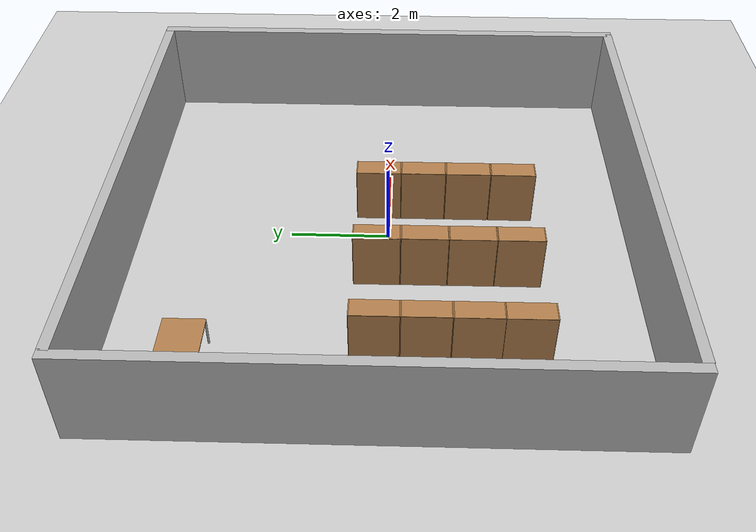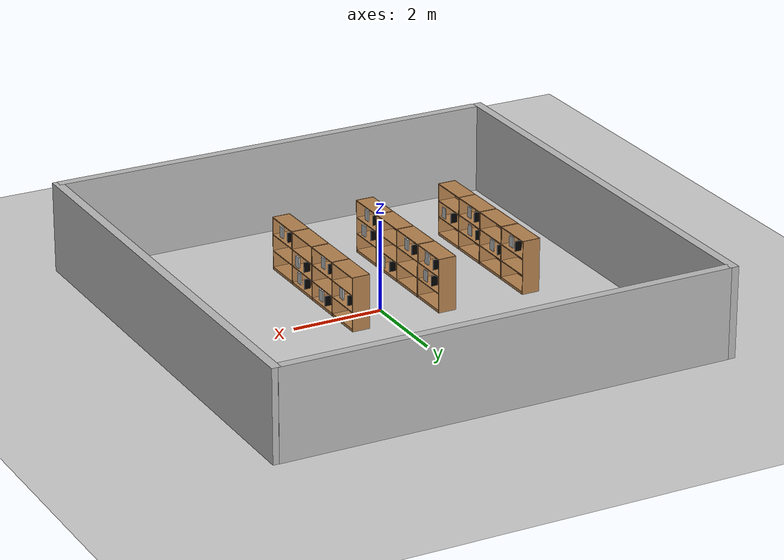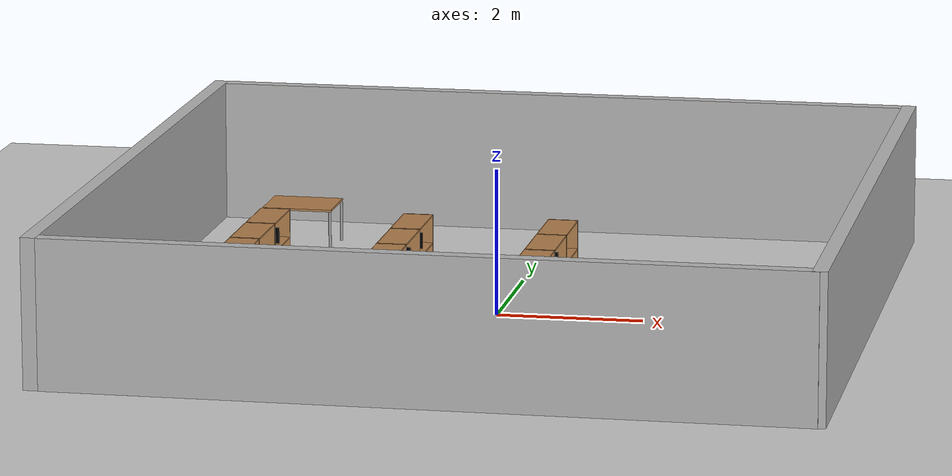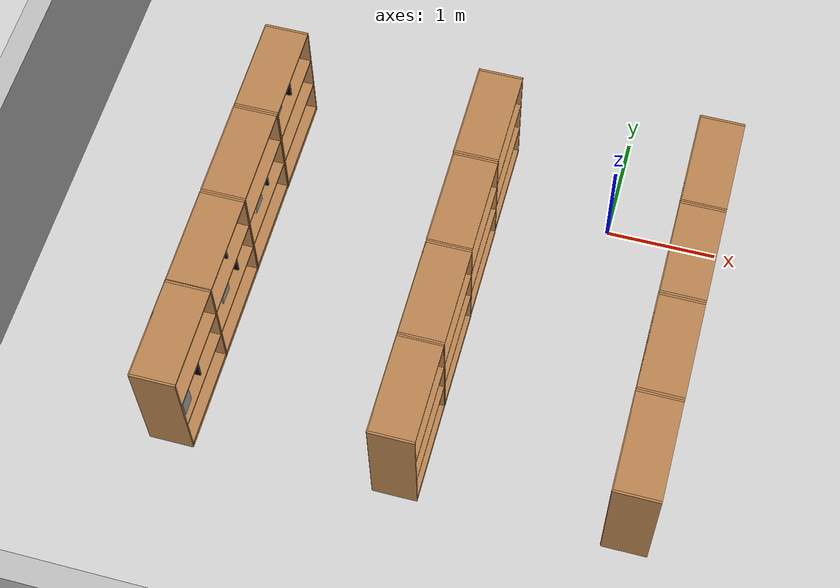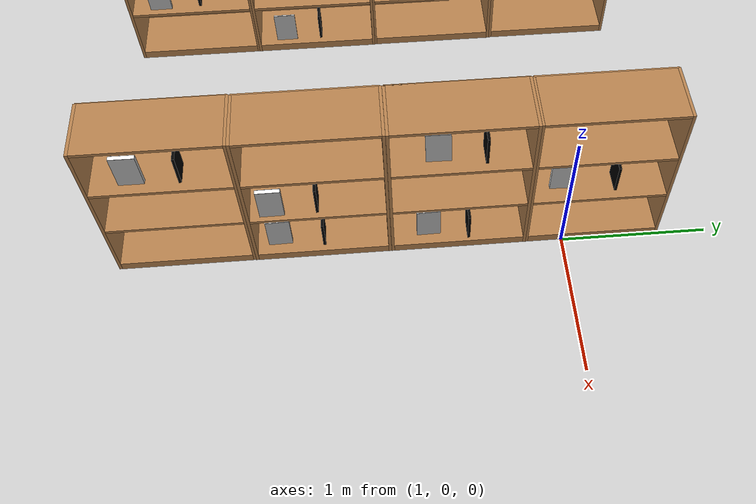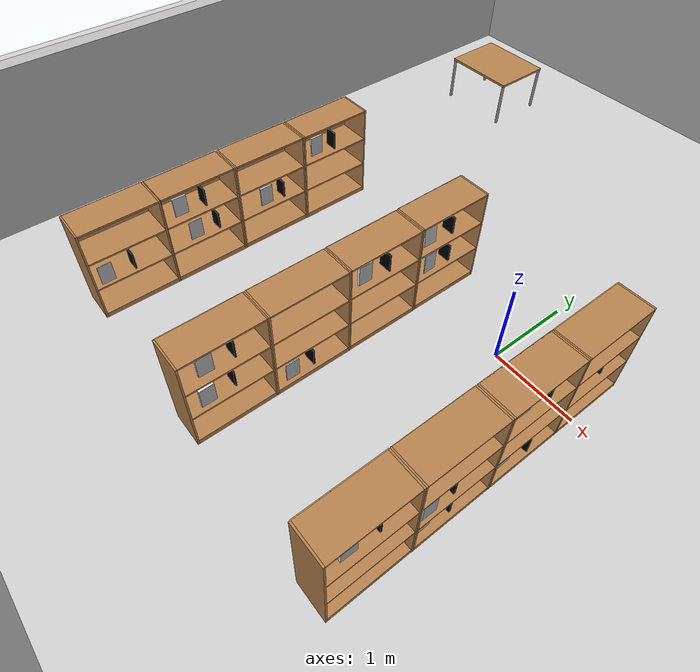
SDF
<sdf version="1.7">
 <world name="default">
  <physics type="ode">
   <ode>
    <solver>
     <type>quick</type>
     <iters>20</iters>
     <sor>1</sor>
     <use_dynamic_moi_rescaling>0</use_dynamic_moi_rescaling>
    </solver>
    <constraints>
     <cfm>0</cfm>
     <erp>0.2</erp>
     <contact_max_correcting_vel>100</contact_max_correcting_vel>
     <contact_surface_layer>0</contact_surface_layer>
    </constraints>
   </ode>
   <real_time_update_rate>1000</real_time_update_rate>
   <max_step_size>0.001</max_step_size>
   <real_time_factor>1</real_time_factor>
  </physics>
  <light name="sun" type="directional">
   <pose>0 0 10 0 -0 0</pose>
   <diffuse>0.8 0.8 0.8 1</diffuse>
   <specular>0.2 0.2 0.2 1</specular>
   <attenuation>
    <range>1000</range>
    <constant>0.9</constant>
    <linear>0.01</linear>
    <quadratic>0.001</quadratic>
   </attenuation>
   <direction>-0.5 0.1 -0.9</direction>
   <spot><inner_angle>0</inner_angle><outer_angle>0</outer_angle><falloff>0</falloff></spot>
  </light>
  <model name="ground_plane">
   <static>1</static>
   <link name="link">
    <collision name="collision">
     <geometry><plane><normal>0 0 1</normal><size>100 100</size></plane></geometry>
     <surface><friction><ode><mu>100</mu><mu2>50</mu2></ode></friction></surface>
    </collision>
    <visual name="visual">
     <cast_shadows>0</cast_shadows>
     <geometry><plane><normal>0 0 1</normal><size>100 100</size></plane></geometry>
     <material>
      <script><uri>file://media/materials/scripts/gazebo.material</uri><name>Gazebo/Grey</name></script>
     </material>
    </visual>
   </link>
  </model>
  <model name="wall_1_model">
   <pose>0 -5 1 0 -0 0</pose>
   <static>1</static>
   <link name="wall_1_body">
    <inertial>
     <mass>1</mass>
     <inertia><ixx>1</ixx><ixy>0</ixy><ixz>0</ixz><iyy>1</iyy><iyz>0</iyz><izz>1</izz></inertia>
    </inertial>
    <collision name="collision"><geometry><box><size>10 0.2 2</size></box></geometry></collision>
    <visual name="visual"><geometry><box><size>10 0.2 2</size></box></geometry></visual>
   </link>
  </model>
  <model name="wall_4_model">
   <pose>5 0.130228 1 0 -0 0</pose>
   <static>1</static>
   <link name="wall_4_body">
    <inertial>
     <mass>1</mass>
     <inertia><ixx>1</ixx><ixy>0</ixy><ixz>0</ixz><iyy>1</iyy><iyz>0</iyz><izz>1</izz></inertia>
    </inertial>
    <collision name="collision"><geometry><box><size>0.2 10.4437 2</size></box></geometry></collision>
    <visual name="visual"><geometry><box><size>0.2 10.4437 2</size></box></geometry></visual>
   </link>
  </model>
  <gravity>0 0 -9.81</gravity>
  <magnetic_field>6e-06 2.3e-05 -4.2e-05</magnetic_field>
  <atmosphere type="adiabatic"/>
  <scene><ambient>0.4 0.4 0.4 1</ambient><background>0.7 0.7 0.7 1</background><shadows>1</shadows></scene>
  <spherical_coordinates>
   <surface_model>EARTH_WGS84</surface_model>
   <latitude_deg>0</latitude_deg>
   <longitude_deg>0</longitude_deg>
   <elevation>0</elevation>
   <heading_deg>0</heading_deg>
  </spherical_coordinates>
  <model name="bookshelf">
   <static>1</static>
   <link name="link">
    <inertial><mass>1</mass></inertial>
    <collision name="back">
     <pose>0 0.005 0.6 0 -0 0</pose>
     <geometry><box><size>0.9 0.01 1.2</size></box></geometry>
    </collision>
    <visual name="visual1">
     <pose>0 0.005 0.6 0 -0 0</pose>
     <geometry><box><size>0.9 0.01 1.2</size></box></geometry>
     <material>
      <script><uri>file://media/materials/scripts/gazebo.material</uri><name>Gazebo/Wood</name></script>
     </material>
    </visual>
    <collision name="left_side">
     <pose>0.45 -0.195 0.6 0 -0 0</pose>
     <geometry><box><size>0.02 0.4 1.2</size></box></geometry>
    </collision>
    <visual name="visual2">
     <pose>0.45 -0.195 0.6 0 -0 0</pose>
     <geometry><box><size>0.02 0.4 1.2</size></box></geometry>
     <material>
      <script><uri>file://media/materials/scripts/gazebo.material</uri><name>Gazebo/Wood</name></script>
     </material>
    </visual>
    <collision name="right_side">
     <pose>-0.45 -0.195 0.6 0 -0 0</pose>
     <geometry><box><size>0.02 0.4 1.2</size></box></geometry>
    </collision>
    <visual name="visual3">
     <pose>-0.45 -0.195 0.6 0 -0 0</pose>
     <geometry><box><size>0.02 0.4 1.2</size></box></geometry>
     <material>
      <script><uri>file://media/materials/scripts/gazebo.material</uri><name>Gazebo/Wood</name></script>
     </material>
    </visual>
    <collision name="bottom">
     <pose>0 -0.195 0.03 0 -0 0</pose>
     <geometry><box><size>0.88 0.4 0.06</size></box></geometry>
    </collision>
    <visual name="visual4">
     <pose>0 -0.195 0.03 0 -0 0</pose>
     <geometry><box><size>0.88 0.4 0.06</size></box></geometry>
     <material>
      <script><uri>file://media/materials/scripts/gazebo.material</uri><name>Gazebo/Wood</name></script>
     </material>
    </visual>
    <collision name="top">
     <pose>0 -0.195 1.19 0 -0 0</pose>
     <geometry><box><size>0.88 0.4 0.02</size></box></geometry>
    </collision>
    <visual name="visual5">
     <pose>0 -0.195 1.19 0 -0 0</pose>
     <geometry><box><size>0.88 0.4 0.02</size></box></geometry>
     <material>
      <script><uri>file://media/materials/scripts/gazebo.material</uri><name>Gazebo/Wood</name></script>
     </material>
    </visual>
    <collision name="low_shelf">
     <pose>0 -0.195 0.43 0 -0 0</pose>
     <geometry><box><size>0.88 0.4 0.02</size></box></geometry>
    </collision>
    <visual name="visual6">
     <pose>0 -0.195 0.43 0 -0 0</pose>
     <geometry><box><size>0.88 0.4 0.02</size></box></geometry>
     <material>
      <script><uri>file://media/materials/scripts/gazebo.material</uri><name>Gazebo/Wood</name></script>
     </material>
    </visual>
    <collision name="high_shelf">
     <pose>0 -0.195 0.8 0 -0 0</pose>
     <geometry><box><size>0.88 0.4 0.02</size></box></geometry>
    </collision>
    <visual name="visual7">
     <pose>0 -0.195 0.8 0 -0 0</pose>
     <geometry><box><size>0.88 0.4 0.02</size></box></geometry>
     <material>
      <script><uri>file://media/materials/scripts/gazebo.material</uri><name>Gazebo/Wood</name></script>
     </material>
    </visual>
   </link>
   <pose>-3.39927 -2.56354 0 0 -0 1.57111</pose>
  </model>
  <model name="bookshelf_clone">
   <static>1</static>
   <link name="link">
    <inertial><mass>1</mass></inertial>
    <collision name="back">
     <pose>0 0.005 0.6 0 -0 0</pose>
     <geometry><box><size>0.9 0.01 1.2</size></box></geometry>
    </collision>
    <visual name="visual1">
     <pose>0 0.005 0.6 0 -0 0</pose>
     <geometry><box><size>0.9 0.01 1.2</size></box></geometry>
     <material>
      <script><uri>file://media/materials/scripts/gazebo.material</uri><name>Gazebo/Wood</name></script>
     </material>
    </visual>
    <collision name="left_side">
     <pose>0.45 -0.195 0.6 0 -0 0</pose>
     <geometry><box><size>0.02 0.4 1.2</size></box></geometry>
    </collision>
    <visual name="visual2">
     <pose>0.45 -0.195 0.6 0 -0 0</pose>
     <geometry><box><size>0.02 0.4 1.2</size></box></geometry>
     <material>
      <script><uri>file://media/materials/scripts/gazebo.material</uri><name>Gazebo/Wood</name></script>
     </material>
    </visual>
    <collision name="right_side">
     <pose>-0.45 -0.195 0.6 0 -0 0</pose>
     <geometry><box><size>0.02 0.4 1.2</size></box></geometry>
    </collision>
    <visual name="visual3">
     <pose>-0.45 -0.195 0.6 0 -0 0</pose>
     <geometry><box><size>0.02 0.4 1.2</size></box></geometry>
     <material>
      <script><uri>file://media/materials/scripts/gazebo.material</uri><name>Gazebo/Wood</name></script>
     </material>
    </visual>
    <collision name="bottom">
     <pose>0 -0.195 0.03 0 -0 0</pose>
     <geometry><box><size>0.88 0.4 0.06</size></box></geometry>
    </collision>
    <visual name="visual4">
     <pose>0 -0.195 0.03 0 -0 0</pose>
     <geometry><box><size>0.88 0.4 0.06</size></box></geometry>
     <material>
      <script><uri>file://media/materials/scripts/gazebo.material</uri><name>Gazebo/Wood</name></script>
     </material>
    </visual>
    <collision name="top">
     <pose>0 -0.195 1.19 0 -0 0</pose>
     <geometry><box><size>0.88 0.4 0.02</size></box></geometry>
    </collision>
    <visual name="visual5">
     <pose>0 -0.195 1.19 0 -0 0</pose>
     <geometry><box><size>0.88 0.4 0.02</size></box></geometry>
     <material>
      <script><uri>file://media/materials/scripts/gazebo.material</uri><name>Gazebo/Wood</name></script>
     </material>
    </visual>
    <collision name="low_shelf">
     <pose>0 -0.195 0.43 0 -0 0</pose>
     <geometry><box><size>0.88 0.4 0.02</size></box></geometry>
    </collision>
    <visual name="visual6">
     <pose>0 -0.195 0.43 0 -0 0</pose>
     <geometry><box><size>0.88 0.4 0.02</size></box></geometry>
     <material>
      <script><uri>file://media/materials/scripts/gazebo.material</uri><name>Gazebo/Wood</name></script>
     </material>
    </visual>
    <collision name="high_shelf">
     <pose>0 -0.195 0.8 0 -0 0</pose>
     <geometry><box><size>0.88 0.4 0.02</size></box></geometry>
    </collision>
    <visual name="visual7">
     <pose>0 -0.195 0.8 0 -0 0</pose>
     <geometry><box><size>0.88 0.4 0.02</size></box></geometry>
     <material>
      <script><uri>file://media/materials/scripts/gazebo.material</uri><name>Gazebo/Wood</name></script>
     </material>
    </visual>
   </link>
   <pose>-3.39982 -1.65685 0 0 -0 1.57111</pose>
  </model>
  <model name="bookshelf_clone_0">
   <static>1</static>
   <link name="link">
    <inertial><mass>1</mass></inertial>
    <collision name="back">
     <pose>0 0.005 0.6 0 -0 0</pose>
     <geometry><box><size>0.9 0.01 1.2</size></box></geometry>
    </collision>
    <visual name="visual1">
     <pose>0 0.005 0.6 0 -0 0</pose>
     <geometry><box><size>0.9 0.01 1.2</size></box></geometry>
     <material>
      <script><uri>file://media/materials/scripts/gazebo.material</uri><name>Gazebo/Wood</name></script>
     </material>
    </visual>
    <collision name="left_side">
     <pose>0.45 -0.195 0.6 0 -0 0</pose>
     <geometry><box><size>0.02 0.4 1.2</size></box></geometry>
    </collision>
    <visual name="visual2">
     <pose>0.45 -0.195 0.6 0 -0 0</pose>
     <geometry><box><size>0.02 0.4 1.2</size></box></geometry>
     <material>
      <script><uri>file://media/materials/scripts/gazebo.material</uri><name>Gazebo/Wood</name></script>
     </material>
    </visual>
    <collision name="right_side">
     <pose>-0.45 -0.195 0.6 0 -0 0</pose>
     <geometry><box><size>0.02 0.4 1.2</size></box></geometry>
    </collision>
    <visual name="visual3">
     <pose>-0.45 -0.195 0.6 0 -0 0</pose>
     <geometry><box><size>0.02 0.4 1.2</size></box></geometry>
     <material>
      <script><uri>file://media/materials/scripts/gazebo.material</uri><name>Gazebo/Wood</name></script>
     </material>
    </visual>
    <collision name="bottom">
     <pose>0 -0.195 0.03 0 -0 0</pose>
     <geometry><box><size>0.88 0.4 0.06</size></box></geometry>
    </collision>
    <visual name="visual4">
     <pose>0 -0.195 0.03 0 -0 0</pose>
     <geometry><box><size>0.88 0.4 0.06</size></box></geometry>
     <material>
      <script><uri>file://media/materials/scripts/gazebo.material</uri><name>Gazebo/Wood</name></script>
     </material>
    </visual>
    <collision name="top">
     <pose>0 -0.195 1.19 0 -0 0</pose>
     <geometry><box><size>0.88 0.4 0.02</size></box></geometry>
    </collision>
    <visual name="visual5">
     <pose>0 -0.195 1.19 0 -0 0</pose>
     <geometry><box><size>0.88 0.4 0.02</size></box></geometry>
     <material>
      <script><uri>file://media/materials/scripts/gazebo.material</uri><name>Gazebo/Wood</name></script>
     </material>
    </visual>
    <collision name="low_shelf">
     <pose>0 -0.195 0.43 0 -0 0</pose>
     <geometry><box><size>0.88 0.4 0.02</size></box></geometry>
    </collision>
    <visual name="visual6">
     <pose>0 -0.195 0.43 0 -0 0</pose>
     <geometry><box><size>0.88 0.4 0.02</size></box></geometry>
     <material>
      <script><uri>file://media/materials/scripts/gazebo.material</uri><name>Gazebo/Wood</name></script>
     </material>
    </visual>
    <collision name="high_shelf">
     <pose>0 -0.195 0.8 0 -0 0</pose>
     <geometry><box><size>0.88 0.4 0.02</size></box></geometry>
    </collision>
    <visual name="visual7">
     <pose>0 -0.195 0.8 0 -0 0</pose>
     <geometry><box><size>0.88 0.4 0.02</size></box></geometry>
     <material>
      <script><uri>file://media/materials/scripts/gazebo.material</uri><name>Gazebo/Wood</name></script>
     </material>
    </visual>
   </link>
   <pose>-3.40087 -0.738465 0 0 -0 1.57111</pose>
  </model>
  <model name="bookshelf_clone_1">
   <static>1</static>
   <link name="link">
    <inertial><mass>1</mass></inertial>
    <collision name="back">
     <pose>0 0.005 0.6 0 -0 0</pose>
     <geometry><box><size>0.9 0.01 1.2</size></box></geometry>
    </collision>
    <visual name="visual1">
     <pose>0 0.005 0.6 0 -0 0</pose>
     <geometry><box><size>0.9 0.01 1.2</size></box></geometry>
     <material>
      <script><uri>file://media/materials/scripts/gazebo.material</uri><name>Gazebo/Wood</name></script>
     </material>
    </visual>
    <collision name="left_side">
     <pose>0.45 -0.195 0.6 0 -0 0</pose>
     <geometry><box><size>0.02 0.4 1.2</size></box></geometry>
    </collision>
    <visual name="visual2">
     <pose>0.45 -0.195 0.6 0 -0 0</pose>
     <geometry><box><size>0.02 0.4 1.2</size></box></geometry>
     <material>
      <script><uri>file://media/materials/scripts/gazebo.material</uri><name>Gazebo/Wood</name></script>
     </material>
    </visual>
    <collision name="right_side">
     <pose>-0.45 -0.195 0.6 0 -0 0</pose>
     <geometry><box><size>0.02 0.4 1.2</size></box></geometry>
    </collision>
    <visual name="visual3">
     <pose>-0.45 -0.195 0.6 0 -0 0</pose>
     <geometry><box><size>0.02 0.4 1.2</size></box></geometry>
     <material>
      <script><uri>file://media/materials/scripts/gazebo.material</uri><name>Gazebo/Wood</name></script>
     </material>
    </visual>
    <collision name="bottom">
     <pose>0 -0.195 0.03 0 -0 0</pose>
     <geometry><box><size>0.88 0.4 0.06</size></box></geometry>
    </collision>
    <visual name="visual4">
     <pose>0 -0.195 0.03 0 -0 0</pose>
     <geometry><box><size>0.88 0.4 0.06</size></box></geometry>
     <material>
      <script><uri>file://media/materials/scripts/gazebo.material</uri><name>Gazebo/Wood</name></script>
     </material>
    </visual>
    <collision name="top">
     <pose>0 -0.195 1.19 0 -0 0</pose>
     <geometry><box><size>0.88 0.4 0.02</size></box></geometry>
    </collision>
    <visual name="visual5">
     <pose>0 -0.195 1.19 0 -0 0</pose>
     <geometry><box><size>0.88 0.4 0.02</size></box></geometry>
     <material>
      <script><uri>file://media/materials/scripts/gazebo.material</uri><name>Gazebo/Wood</name></script>
     </material>
    </visual>
    <collision name="low_shelf">
     <pose>0 -0.195 0.43 0 -0 0</pose>
     <geometry><box><size>0.88 0.4 0.02</size></box></geometry>
    </collision>
    <visual name="visual6">
     <pose>0 -0.195 0.43 0 -0 0</pose>
     <geometry><box><size>0.88 0.4 0.02</size></box></geometry>
     <material>
      <script><uri>file://media/materials/scripts/gazebo.material</uri><name>Gazebo/Wood</name></script>
     </material>
    </visual>
    <collision name="high_shelf">
     <pose>0 -0.195 0.8 0 -0 0</pose>
     <geometry><box><size>0.88 0.4 0.02</size></box></geometry>
    </collision>
    <visual name="visual7">
     <pose>0 -0.195 0.8 0 -0 0</pose>
     <geometry><box><size>0.88 0.4 0.02</size></box></geometry>
     <material>
      <script><uri>file://media/materials/scripts/gazebo.material</uri><name>Gazebo/Wood</name></script>
     </material>
    </visual>
   </link>
   <pose>-3.39929 0.18163 0 0 -0 1.57111</pose>
  </model>
  <model name="bookshelf_clone_2">
   <static>1</static>
   <link name="link">
    <inertial><mass>1</mass></inertial>
    <collision name="back">
     <pose>0 0.005 0.6 0 -0 0</pose>
     <geometry><box><size>0.9 0.01 1.2</size></box></geometry>
    </collision>
    <visual name="visual1">
     <pose>0 0.005 0.6 0 -0 0</pose>
     <geometry><box><size>0.9 0.01 1.2</size></box></geometry>
     <material>
      <script><uri>file://media/materials/scripts/gazebo.material</uri><name>Gazebo/Wood</name></script>
     </material>
    </visual>
    <collision name="left_side">
     <pose>0.45 -0.195 0.6 0 -0 0</pose>
     <geometry><box><size>0.02 0.4 1.2</size></box></geometry>
    </collision>
    <visual name="visual2">
     <pose>0.45 -0.195 0.6 0 -0 0</pose>
     <geometry><box><size>0.02 0.4 1.2</size></box></geometry>
     <material>
      <script><uri>file://media/materials/scripts/gazebo.material</uri><name>Gazebo/Wood</name></script>
     </material>
    </visual>
    <collision name="right_side">
     <pose>-0.45 -0.195 0.6 0 -0 0</pose>
     <geometry><box><size>0.02 0.4 1.2</size></box></geometry>
    </collision>
    <visual name="visual3">
     <pose>-0.45 -0.195 0.6 0 -0 0</pose>
     <geometry><box><size>0.02 0.4 1.2</size></box></geometry>
     <material>
      <script><uri>file://media/materials/scripts/gazebo.material</uri><name>Gazebo/Wood</name></script>
     </material>
    </visual>
    <collision name="bottom">
     <pose>0 -0.195 0.03 0 -0 0</pose>
     <geometry><box><size>0.88 0.4 0.06</size></box></geometry>
    </collision>
    <visual name="visual4">
     <pose>0 -0.195 0.03 0 -0 0</pose>
     <geometry><box><size>0.88 0.4 0.06</size></box></geometry>
     <material>
      <script><uri>file://media/materials/scripts/gazebo.material</uri><name>Gazebo/Wood</name></script>
     </material>
    </visual>
    <collision name="top">
     <pose>0 -0.195 1.19 0 -0 0</pose>
     <geometry><box><size>0.88 0.4 0.02</size></box></geometry>
    </collision>
    <visual name="visual5">
     <pose>0 -0.195 1.19 0 -0 0</pose>
     <geometry><box><size>0.88 0.4 0.02</size></box></geometry>
     <material>
      <script><uri>file://media/materials/scripts/gazebo.material</uri><name>Gazebo/Wood</name></script>
     </material>
    </visual>
    <collision name="low_shelf">
     <pose>0 -0.195 0.43 0 -0 0</pose>
     <geometry><box><size>0.88 0.4 0.02</size></box></geometry>
    </collision>
    <visual name="visual6">
     <pose>0 -0.195 0.43 0 -0 0</pose>
     <geometry><box><size>0.88 0.4 0.02</size></box></geometry>
     <material>
      <script><uri>file://media/materials/scripts/gazebo.material</uri><name>Gazebo/Wood</name></script>
     </material>
    </visual>
    <collision name="high_shelf">
     <pose>0 -0.195 0.8 0 -0 0</pose>
     <geometry><box><size>0.88 0.4 0.02</size></box></geometry>
    </collision>
    <visual name="visual7">
     <pose>0 -0.195 0.8 0 -0 0</pose>
     <geometry><box><size>0.88 0.4 0.02</size></box></geometry>
     <material>
      <script><uri>file://media/materials/scripts/gazebo.material</uri><name>Gazebo/Wood</name></script>
     </material>
    </visual>
   </link>
   <pose>-1.39561 -2.55264 0 0 -0 1.57111</pose>
  </model>
  <model name="bookshelf_clone_3">
   <static>1</static>
   <link name="link">
    <inertial><mass>1</mass></inertial>
    <collision name="back">
     <pose>0 0.005 0.6 0 -0 0</pose>
     <geometry><box><size>0.9 0.01 1.2</size></box></geometry>
    </collision>
    <visual name="visual1">
     <pose>0 0.005 0.6 0 -0 0</pose>
     <geometry><box><size>0.9 0.01 1.2</size></box></geometry>
     <material>
      <script><uri>file://media/materials/scripts/gazebo.material</uri><name>Gazebo/Wood</name></script>
     </material>
    </visual>
    <collision name="left_side">
     <pose>0.45 -0.195 0.6 0 -0 0</pose>
     <geometry><box><size>0.02 0.4 1.2</size></box></geometry>
    </collision>
    <visual name="visual2">
     <pose>0.45 -0.195 0.6 0 -0 0</pose>
     <geometry><box><size>0.02 0.4 1.2</size></box></geometry>
     <material>
      <script><uri>file://media/materials/scripts/gazebo.material</uri><name>Gazebo/Wood</name></script>
     </material>
    </visual>
    <collision name="right_side">
     <pose>-0.45 -0.195 0.6 0 -0 0</pose>
     <geometry><box><size>0.02 0.4 1.2</size></box></geometry>
    </collision>
    <visual name="visual3">
     <pose>-0.45 -0.195 0.6 0 -0 0</pose>
     <geometry><box><size>0.02 0.4 1.2</size></box></geometry>
     <material>
      <script><uri>file://media/materials/scripts/gazebo.material</uri><name>Gazebo/Wood</name></script>
     </material>
    </visual>
    <collision name="bottom">
     <pose>0 -0.195 0.03 0 -0 0</pose>
     <geometry><box><size>0.88 0.4 0.06</size></box></geometry>
    </collision>
    <visual name="visual4">
     <pose>0 -0.195 0.03 0 -0 0</pose>
     <geometry><box><size>0.88 0.4 0.06</size></box></geometry>
     <material>
      <script><uri>file://media/materials/scripts/gazebo.material</uri><name>Gazebo/Wood</name></script>
     </material>
    </visual>
    <collision name="top">
     <pose>0 -0.195 1.19 0 -0 0</pose>
     <geometry><box><size>0.88 0.4 0.02</size></box></geometry>
    </collision>
    <visual name="visual5">
     <pose>0 -0.195 1.19 0 -0 0</pose>
     <geometry><box><size>0.88 0.4 0.02</size></box></geometry>
     <material>
      <script><uri>file://media/materials/scripts/gazebo.material</uri><name>Gazebo/Wood</name></script>
     </material>
    </visual>
    <collision name="low_shelf">
     <pose>0 -0.195 0.43 0 -0 0</pose>
     <geometry><box><size>0.88 0.4 0.02</size></box></geometry>
    </collision>
    <visual name="visual6">
     <pose>0 -0.195 0.43 0 -0 0</pose>
     <geometry><box><size>0.88 0.4 0.02</size></box></geometry>
     <material>
      <script><uri>file://media/materials/scripts/gazebo.material</uri><name>Gazebo/Wood</name></script>
     </material>
    </visual>
    <collision name="high_shelf">
     <pose>0 -0.195 0.8 0 -0 0</pose>
     <geometry><box><size>0.88 0.4 0.02</size></box></geometry>
    </collision>
    <visual name="visual7">
     <pose>0 -0.195 0.8 0 -0 0</pose>
     <geometry><box><size>0.88 0.4 0.02</size></box></geometry>
     <material>
      <script><uri>file://media/materials/scripts/gazebo.material</uri><name>Gazebo/Wood</name></script>
     </material>
    </visual>
   </link>
   <pose>-1.39572 -1.63764 0 0 -0 1.57111</pose>
  </model>
  <model name="bookshelf_clone_4">
   <static>1</static>
   <link name="link">
    <inertial><mass>1</mass></inertial>
    <collision name="back">
     <pose>0 0.005 0.6 0 -0 0</pose>
     <geometry><box><size>0.9 0.01 1.2</size></box></geometry>
    </collision>
    <visual name="visual1">
     <pose>0 0.005 0.6 0 -0 0</pose>
     <geometry><box><size>0.9 0.01 1.2</size></box></geometry>
     <material>
      <script><uri>file://media/materials/scripts/gazebo.material</uri><name>Gazebo/Wood</name></script>
     </material>
    </visual>
    <collision name="left_side">
     <pose>0.45 -0.195 0.6 0 -0 0</pose>
     <geometry><box><size>0.02 0.4 1.2</size></box></geometry>
    </collision>
    <visual name="visual2">
     <pose>0.45 -0.195 0.6 0 -0 0</pose>
     <geometry><box><size>0.02 0.4 1.2</size></box></geometry>
     <material>
      <script><uri>file://media/materials/scripts/gazebo.material</uri><name>Gazebo/Wood</name></script>
     </material>
    </visual>
    <collision name="right_side">
     <pose>-0.45 -0.195 0.6 0 -0 0</pose>
     <geometry><box><size>0.02 0.4 1.2</size></box></geometry>
    </collision>
    <visual name="visual3">
     <pose>-0.45 -0.195 0.6 0 -0 0</pose>
     <geometry><box><size>0.02 0.4 1.2</size></box></geometry>
     <material>
      <script><uri>file://media/materials/scripts/gazebo.material</uri><name>Gazebo/Wood</name></script>
     </material>
    </visual>
    <collision name="bottom">
     <pose>0 -0.195 0.03 0 -0 0</pose>
     <geometry><box><size>0.88 0.4 0.06</size></box></geometry>
    </collision>
    <visual name="visual4">
     <pose>0 -0.195 0.03 0 -0 0</pose>
     <geometry><box><size>0.88 0.4 0.06</size></box></geometry>
     <material>
      <script><uri>file://media/materials/scripts/gazebo.material</uri><name>Gazebo/Wood</name></script>
     </material>
    </visual>
    <collision name="top">
     <pose>0 -0.195 1.19 0 -0 0</pose>
     <geometry><box><size>0.88 0.4 0.02</size></box></geometry>
    </collision>
    <visual name="visual5">
     <pose>0 -0.195 1.19 0 -0 0</pose>
     <geometry><box><size>0.88 0.4 0.02</size></box></geometry>
     <material>
      <script><uri>file://media/materials/scripts/gazebo.material</uri><name>Gazebo/Wood</name></script>
     </material>
    </visual>
    <collision name="low_shelf">
     <pose>0 -0.195 0.43 0 -0 0</pose>
     <geometry><box><size>0.88 0.4 0.02</size></box></geometry>
    </collision>
    <visual name="visual6">
     <pose>0 -0.195 0.43 0 -0 0</pose>
     <geometry><box><size>0.88 0.4 0.02</size></box></geometry>
     <material>
      <script><uri>file://media/materials/scripts/gazebo.material</uri><name>Gazebo/Wood</name></script>
     </material>
    </visual>
    <collision name="high_shelf">
     <pose>0 -0.195 0.8 0 -0 0</pose>
     <geometry><box><size>0.88 0.4 0.02</size></box></geometry>
    </collision>
    <visual name="visual7">
     <pose>0 -0.195 0.8 0 -0 0</pose>
     <geometry><box><size>0.88 0.4 0.02</size></box></geometry>
     <material>
      <script><uri>file://media/materials/scripts/gazebo.material</uri><name>Gazebo/Wood</name></script>
     </material>
    </visual>
   </link>
   <pose>-1.39871 -0.721952 0 0 -0 1.57111</pose>
  </model>
  <model name="bookshelf_clone_5">
   <static>1</static>
   <link name="link">
    <inertial><mass>1</mass></inertial>
    <collision name="back">
     <pose>0 0.005 0.6 0 -0 0</pose>
     <geometry><box><size>0.9 0.01 1.2</size></box></geometry>
    </collision>
    <visual name="visual1">
     <pose>0 0.005 0.6 0 -0 0</pose>
     <geometry><box><size>0.9 0.01 1.2</size></box></geometry>
     <material>
      <script><uri>file://media/materials/scripts/gazebo.material</uri><name>Gazebo/Wood</name></script>
     </material>
    </visual>
    <collision name="left_side">
     <pose>0.45 -0.195 0.6 0 -0 0</pose>
     <geometry><box><size>0.02 0.4 1.2</size></box></geometry>
    </collision>
    <visual name="visual2">
     <pose>0.45 -0.195 0.6 0 -0 0</pose>
     <geometry><box><size>0.02 0.4 1.2</size></box></geometry>
     <material>
      <script><uri>file://media/materials/scripts/gazebo.material</uri><name>Gazebo/Wood</name></script>
     </material>
    </visual>
    <collision name="right_side">
     <pose>-0.45 -0.195 0.6 0 -0 0</pose>
     <geometry><box><size>0.02 0.4 1.2</size></box></geometry>
    </collision>
    <visual name="visual3">
     <pose>-0.45 -0.195 0.6 0 -0 0</pose>
     <geometry><box><size>0.02 0.4 1.2</size></box></geometry>
     <material>
      <script><uri>file://media/materials/scripts/gazebo.material</uri><name>Gazebo/Wood</name></script>
     </material>
    </visual>
    <collision name="bottom">
     <pose>0 -0.195 0.03 0 -0 0</pose>
     <geometry><box><size>0.88 0.4 0.06</size></box></geometry>
    </collision>
    <visual name="visual4">
     <pose>0 -0.195 0.03 0 -0 0</pose>
     <geometry><box><size>0.88 0.4 0.06</size></box></geometry>
     <material>
      <script><uri>file://media/materials/scripts/gazebo.material</uri><name>Gazebo/Wood</name></script>
     </material>
    </visual>
    <collision name="top">
     <pose>0 -0.195 1.19 0 -0 0</pose>
     <geometry><box><size>0.88 0.4 0.02</size></box></geometry>
    </collision>
    <visual name="visual5">
     <pose>0 -0.195 1.19 0 -0 0</pose>
     <geometry><box><size>0.88 0.4 0.02</size></box></geometry>
     <material>
      <script><uri>file://media/materials/scripts/gazebo.material</uri><name>Gazebo/Wood</name></script>
     </material>
    </visual>
    <collision name="low_shelf">
     <pose>0 -0.195 0.43 0 -0 0</pose>
     <geometry><box><size>0.88 0.4 0.02</size></box></geometry>
    </collision>
    <visual name="visual6">
     <pose>0 -0.195 0.43 0 -0 0</pose>
     <geometry><box><size>0.88 0.4 0.02</size></box></geometry>
     <material>
      <script><uri>file://media/materials/scripts/gazebo.material</uri><name>Gazebo/Wood</name></script>
     </material>
    </visual>
    <collision name="high_shelf">
     <pose>0 -0.195 0.8 0 -0 0</pose>
     <geometry><box><size>0.88 0.4 0.02</size></box></geometry>
    </collision>
    <visual name="visual7">
     <pose>0 -0.195 0.8 0 -0 0</pose>
     <geometry><box><size>0.88 0.4 0.02</size></box></geometry>
     <material>
      <script><uri>file://media/materials/scripts/gazebo.material</uri><name>Gazebo/Wood</name></script>
     </material>
    </visual>
   </link>
   <pose>-1.40262 0.198766 0 0 -0 1.57111</pose>
  </model>
  <model name="bookshelf_clone_6">
   <static>1</static>
   <link name="link">
    <inertial><mass>1</mass></inertial>
    <collision name="back">
     <pose>0 0.005 0.6 0 -0 0</pose>
     <geometry><box><size>0.9 0.01 1.2</size></box></geometry>
    </collision>
    <visual name="visual1">
     <pose>0 0.005 0.6 0 -0 0</pose>
     <geometry><box><size>0.9 0.01 1.2</size></box></geometry>
     <material>
      <script><uri>file://media/materials/scripts/gazebo.material</uri><name>Gazebo/Wood</name></script>
     </material>
    </visual>
    <collision name="left_side">
     <pose>0.45 -0.195 0.6 0 -0 0</pose>
     <geometry><box><size>0.02 0.4 1.2</size></box></geometry>
    </collision>
    <visual name="visual2">
     <pose>0.45 -0.195 0.6 0 -0 0</pose>
     <geometry><box><size>0.02 0.4 1.2</size></box></geometry>
     <material>
      <script><uri>file://media/materials/scripts/gazebo.material</uri><name>Gazebo/Wood</name></script>
     </material>
    </visual>
    <collision name="right_side">
     <pose>-0.45 -0.195 0.6 0 -0 0</pose>
     <geometry><box><size>0.02 0.4 1.2</size></box></geometry>
    </collision>
    <visual name="visual3">
     <pose>-0.45 -0.195 0.6 0 -0 0</pose>
     <geometry><box><size>0.02 0.4 1.2</size></box></geometry>
     <material>
      <script><uri>file://media/materials/scripts/gazebo.material</uri><name>Gazebo/Wood</name></script>
     </material>
    </visual>
    <collision name="bottom">
     <pose>0 -0.195 0.03 0 -0 0</pose>
     <geometry><box><size>0.88 0.4 0.06</size></box></geometry>
    </collision>
    <visual name="visual4">
     <pose>0 -0.195 0.03 0 -0 0</pose>
     <geometry><box><size>0.88 0.4 0.06</size></box></geometry>
     <material>
      <script><uri>file://media/materials/scripts/gazebo.material</uri><name>Gazebo/Wood</name></script>
     </material>
    </visual>
    <collision name="top">
     <pose>0 -0.195 1.19 0 -0 0</pose>
     <geometry><box><size>0.88 0.4 0.02</size></box></geometry>
    </collision>
    <visual name="visual5">
     <pose>0 -0.195 1.19 0 -0 0</pose>
     <geometry><box><size>0.88 0.4 0.02</size></box></geometry>
     <material>
      <script><uri>file://media/materials/scripts/gazebo.material</uri><name>Gazebo/Wood</name></script>
     </material>
    </visual>
    <collision name="low_shelf">
     <pose>0 -0.195 0.43 0 -0 0</pose>
     <geometry><box><size>0.88 0.4 0.02</size></box></geometry>
    </collision>
    <visual name="visual6">
     <pose>0 -0.195 0.43 0 -0 0</pose>
     <geometry><box><size>0.88 0.4 0.02</size></box></geometry>
     <material>
      <script><uri>file://media/materials/scripts/gazebo.material</uri><name>Gazebo/Wood</name></script>
     </material>
    </visual>
    <collision name="high_shelf">
     <pose>0 -0.195 0.8 0 -0 0</pose>
     <geometry><box><size>0.88 0.4 0.02</size></box></geometry>
    </collision>
    <visual name="visual7">
     <pose>0 -0.195 0.8 0 -0 0</pose>
     <geometry><box><size>0.88 0.4 0.02</size></box></geometry>
     <material>
      <script><uri>file://media/materials/scripts/gazebo.material</uri><name>Gazebo/Wood</name></script>
     </material>
    </visual>
   </link>
   <pose>0.599473 -2.54348 0 0 -0 1.57111</pose>
  </model>
  <model name="bookshelf_clone_7">
   <static>1</static>
   <link name="link">
    <inertial><mass>1</mass></inertial>
    <collision name="back">
     <pose>0 0.005 0.6 0 -0 0</pose>
     <geometry><box><size>0.9 0.01 1.2</size></box></geometry>
    </collision>
    <visual name="visual1">
     <pose>0 0.005 0.6 0 -0 0</pose>
     <geometry><box><size>0.9 0.01 1.2</size></box></geometry>
     <material>
      <script><uri>file://media/materials/scripts/gazebo.material</uri><name>Gazebo/Wood</name></script>
     </material>
    </visual>
    <collision name="left_side">
     <pose>0.45 -0.195 0.6 0 -0 0</pose>
     <geometry><box><size>0.02 0.4 1.2</size></box></geometry>
    </collision>
    <visual name="visual2">
     <pose>0.45 -0.195 0.6 0 -0 0</pose>
     <geometry><box><size>0.02 0.4 1.2</size></box></geometry>
     <material>
      <script><uri>file://media/materials/scripts/gazebo.material</uri><name>Gazebo/Wood</name></script>
     </material>
    </visual>
    <collision name="right_side">
     <pose>-0.45 -0.195 0.6 0 -0 0</pose>
     <geometry><box><size>0.02 0.4 1.2</size></box></geometry>
    </collision>
    <visual name="visual3">
     <pose>-0.45 -0.195 0.6 0 -0 0</pose>
     <geometry><box><size>0.02 0.4 1.2</size></box></geometry>
     <material>
      <script><uri>file://media/materials/scripts/gazebo.material</uri><name>Gazebo/Wood</name></script>
     </material>
    </visual>
    <collision name="bottom">
     <pose>0 -0.195 0.03 0 -0 0</pose>
     <geometry><box><size>0.88 0.4 0.06</size></box></geometry>
    </collision>
    <visual name="visual4">
     <pose>0 -0.195 0.03 0 -0 0</pose>
     <geometry><box><size>0.88 0.4 0.06</size></box></geometry>
     <material>
      <script><uri>file://media/materials/scripts/gazebo.material</uri><name>Gazebo/Wood</name></script>
     </material>
    </visual>
    <collision name="top">
     <pose>0 -0.195 1.19 0 -0 0</pose>
     <geometry><box><size>0.88 0.4 0.02</size></box></geometry>
    </collision>
    <visual name="visual5">
     <pose>0 -0.195 1.19 0 -0 0</pose>
     <geometry><box><size>0.88 0.4 0.02</size></box></geometry>
     <material>
      <script><uri>file://media/materials/scripts/gazebo.material</uri><name>Gazebo/Wood</name></script>
     </material>
    </visual>
    <collision name="low_shelf">
     <pose>0 -0.195 0.43 0 -0 0</pose>
     <geometry><box><size>0.88 0.4 0.02</size></box></geometry>
    </collision>
    <visual name="visual6">
     <pose>0 -0.195 0.43 0 -0 0</pose>
     <geometry><box><size>0.88 0.4 0.02</size></box></geometry>
     <material>
      <script><uri>file://media/materials/scripts/gazebo.material</uri><name>Gazebo/Wood</name></script>
     </material>
    </visual>
    <collision name="high_shelf">
     <pose>0 -0.195 0.8 0 -0 0</pose>
     <geometry><box><size>0.88 0.4 0.02</size></box></geometry>
    </collision>
    <visual name="visual7">
     <pose>0 -0.195 0.8 0 -0 0</pose>
     <geometry><box><size>0.88 0.4 0.02</size></box></geometry>
     <material>
      <script><uri>file://media/materials/scripts/gazebo.material</uri><name>Gazebo/Wood</name></script>
     </material>
    </visual>
   </link>
   <pose>0.600978 -1.62562 0 0 -0 1.57111</pose>
  </model>
  <model name="bookshelf_clone_8">
   <static>1</static>
   <link name="link">
    <inertial><mass>1</mass></inertial>
    <collision name="back">
     <pose>0 0.005 0.6 0 -0 0</pose>
     <geometry><box><size>0.9 0.01 1.2</size></box></geometry>
    </collision>
    <visual name="visual1">
     <pose>0 0.005 0.6 0 -0 0</pose>
     <geometry><box><size>0.9 0.01 1.2</size></box></geometry>
     <material>
      <script><uri>file://media/materials/scripts/gazebo.material</uri><name>Gazebo/Wood</name></script>
     </material>
    </visual>
    <collision name="left_side">
     <pose>0.45 -0.195 0.6 0 -0 0</pose>
     <geometry><box><size>0.02 0.4 1.2</size></box></geometry>
    </collision>
    <visual name="visual2">
     <pose>0.45 -0.195 0.6 0 -0 0</pose>
     <geometry><box><size>0.02 0.4 1.2</size></box></geometry>
     <material>
      <script><uri>file://media/materials/scripts/gazebo.material</uri><name>Gazebo/Wood</name></script>
     </material>
    </visual>
    <collision name="right_side">
     <pose>-0.45 -0.195 0.6 0 -0 0</pose>
     <geometry><box><size>0.02 0.4 1.2</size></box></geometry>
    </collision>
    <visual name="visual3">
     <pose>-0.45 -0.195 0.6 0 -0 0</pose>
     <geometry><box><size>0.02 0.4 1.2</size></box></geometry>
     <material>
      <script><uri>file://media/materials/scripts/gazebo.material</uri><name>Gazebo/Wood</name></script>
     </material>
    </visual>
    <collision name="bottom">
     <pose>0 -0.195 0.03 0 -0 0</pose>
     <geometry><box><size>0.88 0.4 0.06</size></box></geometry>
    </collision>
    <visual name="visual4">
     <pose>0 -0.195 0.03 0 -0 0</pose>
     <geometry><box><size>0.88 0.4 0.06</size></box></geometry>
     <material>
      <script><uri>file://media/materials/scripts/gazebo.material</uri><name>Gazebo/Wood</name></script>
     </material>
    </visual>
    <collision name="top">
     <pose>0 -0.195 1.19 0 -0 0</pose>
     <geometry><box><size>0.88 0.4 0.02</size></box></geometry>
    </collision>
    <visual name="visual5">
     <pose>0 -0.195 1.19 0 -0 0</pose>
     <geometry><box><size>0.88 0.4 0.02</size></box></geometry>
     <material>
      <script><uri>file://media/materials/scripts/gazebo.material</uri><name>Gazebo/Wood</name></script>
     </material>
    </visual>
    <collision name="low_shelf">
     <pose>0 -0.195 0.43 0 -0 0</pose>
     <geometry><box><size>0.88 0.4 0.02</size></box></geometry>
    </collision>
    <visual name="visual6">
     <pose>0 -0.195 0.43 0 -0 0</pose>
     <geometry><box><size>0.88 0.4 0.02</size></box></geometry>
     <material>
      <script><uri>file://media/materials/scripts/gazebo.material</uri><name>Gazebo/Wood</name></script>
     </material>
    </visual>
    <collision name="high_shelf">
     <pose>0 -0.195 0.8 0 -0 0</pose>
     <geometry><box><size>0.88 0.4 0.02</size></box></geometry>
    </collision>
    <visual name="visual7">
     <pose>0 -0.195 0.8 0 -0 0</pose>
     <geometry><box><size>0.88 0.4 0.02</size></box></geometry>
     <material>
      <script><uri>file://media/materials/scripts/gazebo.material</uri><name>Gazebo/Wood</name></script>
     </material>
    </visual>
   </link>
   <pose>0.601754 -0.705437 0 0 -0 1.57111</pose>
  </model>
  <model name="bookshelf_clone_9">
   <static>1</static>
   <link name="link">
    <inertial><mass>1</mass></inertial>
    <collision name="back">
     <pose>0 0.005 0.6 0 -0 0</pose>
     <geometry><box><size>0.9 0.01 1.2</size></box></geometry>
    </collision>
    <visual name="visual1">
     <pose>0 0.005 0.6 0 -0 0</pose>
     <geometry><box><size>0.9 0.01 1.2</size></box></geometry>
     <material>
      <script><uri>file://media/materials/scripts/gazebo.material</uri><name>Gazebo/Wood</name></script>
     </material>
    </visual>
    <collision name="left_side">
     <pose>0.45 -0.195 0.6 0 -0 0</pose>
     <geometry><box><size>0.02 0.4 1.2</size></box></geometry>
    </collision>
    <visual name="visual2">
     <pose>0.45 -0.195 0.6 0 -0 0</pose>
     <geometry><box><size>0.02 0.4 1.2</size></box></geometry>
     <material>
      <script><uri>file://media/materials/scripts/gazebo.material</uri><name>Gazebo/Wood</name></script>
     </material>
    </visual>
    <collision name="right_side">
     <pose>-0.45 -0.195 0.6 0 -0 0</pose>
     <geometry><box><size>0.02 0.4 1.2</size></box></geometry>
    </collision>
    <visual name="visual3">
     <pose>-0.45 -0.195 0.6 0 -0 0</pose>
     <geometry><box><size>0.02 0.4 1.2</size></box></geometry>
     <material>
      <script><uri>file://media/materials/scripts/gazebo.material</uri><name>Gazebo/Wood</name></script>
     </material>
    </visual>
    <collision name="bottom">
     <pose>0 -0.195 0.03 0 -0 0</pose>
     <geometry><box><size>0.88 0.4 0.06</size></box></geometry>
    </collision>
    <visual name="visual4">
     <pose>0 -0.195 0.03 0 -0 0</pose>
     <geometry><box><size>0.88 0.4 0.06</size></box></geometry>
     <material>
      <script><uri>file://media/materials/scripts/gazebo.material</uri><name>Gazebo/Wood</name></script>
     </material>
    </visual>
    <collision name="top">
     <pose>0 -0.195 1.19 0 -0 0</pose>
     <geometry><box><size>0.88 0.4 0.02</size></box></geometry>
    </collision>
    <visual name="visual5">
     <pose>0 -0.195 1.19 0 -0 0</pose>
     <geometry><box><size>0.88 0.4 0.02</size></box></geometry>
     <material>
      <script><uri>file://media/materials/scripts/gazebo.material</uri><name>Gazebo/Wood</name></script>
     </material>
    </visual>
    <collision name="low_shelf">
     <pose>0 -0.195 0.43 0 -0 0</pose>
     <geometry><box><size>0.88 0.4 0.02</size></box></geometry>
    </collision>
    <visual name="visual6">
     <pose>0 -0.195 0.43 0 -0 0</pose>
     <geometry><box><size>0.88 0.4 0.02</size></box></geometry>
     <material>
      <script><uri>file://media/materials/scripts/gazebo.material</uri><name>Gazebo/Wood</name></script>
     </material>
    </visual>
    <collision name="high_shelf">
     <pose>0 -0.195 0.8 0 -0 0</pose>
     <geometry><box><size>0.88 0.4 0.02</size></box></geometry>
    </collision>
    <visual name="visual7">
     <pose>0 -0.195 0.8 0 -0 0</pose>
     <geometry><box><size>0.88 0.4 0.02</size></box></geometry>
     <material>
      <script><uri>file://media/materials/scripts/gazebo.material</uri><name>Gazebo/Wood</name></script>
     </material>
    </visual>
   </link>
   <pose>0.601436 0.210613 0 0 -0 1.57111</pose>
  </model>
  <model name="book_1">
   <link name="cover">
    <pose>0 -0.000108 0.015405 0 -0 0</pose>
    <visual name="visual">
     <geometry><box><size>0.245 0.16 0.03</size></box></geometry>
     <material>
      <script>
       <uri>file:///home/bruno/Downloads/lib_world_models/book_1/materials/scripts</uri>
       <uri>file:///home/bruno/Downloads/lib_world_models/book_1/materials/textures</uri>
       <name>book_1</name>
      </script>
     </material>
    </visual>
    <collision name="collision"><geometry><box><size>0.245 0.16 0.03</size></box></geometry></collision>
   </link>
   <link name="page">
    <pose>0 0.000608 0.015405 0 -0 0</pose>
    <visual name="visual">
     <geometry><box><size>0.24502 0.15862 0.028</size></box></geometry>
     <material>
      <lighting>1</lighting>
      <ambient>1 1 1 1</ambient>
      <diffuse>1 1 1 1</diffuse>
      <specular>0.01 0.01 0.01 1</specular>
      <emissive>0 0 0 1</emissive>
      <shader type="vertex"><normal_map>__default__</normal_map></shader>
     </material>
    </visual>
    <collision name="collision"><geometry><box><size>0.245 0.16 0.03</size></box></geometry></collision>
   </link>
   <static>1</static>
   <pose>0.896361 -2.72547 0.935973 -2.42723 -1.55442 -0.725508</pose>
  </model>
  <model name="book_10">
   <link name="cover">
    <pose>0 -0.000108 0.015405 0 -0 0</pose>
    <visual name="visual">
     <geometry><box><size>0.245 0.16 0.03</size></box></geometry>
     <material>
      <script>
       <uri>file:///home/bruno/Downloads/lib_world_models/book_10/materials/scripts</uri>
       <uri>file:///home/bruno/Downloads/lib_world_models/book_10/materials/textures</uri>
       <name>book_10</name>
      </script>
     </material>
    </visual>
    <collision name="collision"><geometry><box><size>0.245 0.16 0.03</size></box></geometry></collision>
   </link>
   <link name="page">
    <pose>0 0.000608 0.015405 0 -0 0</pose>
    <visual name="visual">
     <geometry><box><size>0.24502 0.15862 0.028</size></box></geometry>
     <material>
      <lighting>1</lighting>
      <ambient>1 1 1 1</ambient>
      <diffuse>1 1 1 1</diffuse>
      <specular>0.01 0.01 0.01 1</specular>
      <emissive>0 0 0 1</emissive>
      <shader type="vertex"><normal_map>__default__</normal_map></shader>
     </material>
    </visual>
    <collision name="collision"><geometry><box><size>0.245 0.16 0.03</size></box></geometry></collision>
   </link>
   <static>1</static>
   <pose>0.930987 -1.92081 0.562801 -3.14159 -1.56734 0.006937</pose>
  </model>
  <model name="book_11">
   <link name="cover">
    <pose>0 -0.000108 0.015405 0 -0 0</pose>
    <visual name="visual">
     <geometry><box><size>0.245 0.16 0.03</size></box></geometry>
     <material>
      <script>
       <uri>file:///home/bruno/Downloads/lib_world_models/book_11/materials/scripts</uri>
       <uri>file:///home/bruno/Downloads/lib_world_models/book_11/materials/textures</uri>
       <name>book_11</name>
      </script>
     </material>
    </visual>
    <collision name="collision"><geometry><box><size>0.245 0.16 0.03</size></box></geometry></collision>
   </link>
   <link name="page">
    <pose>0 0.000608 0.015405 0 -0 0</pose>
    <visual name="visual">
     <geometry><box><size>0.24502 0.15862 0.028</size></box></geometry>
     <material>
      <lighting>1</lighting>
      <ambient>1 1 1 1</ambient>
      <diffuse>1 1 1 1</diffuse>
      <specular>0.01 0.01 0.01 1</specular>
      <emissive>0 0 0 1</emissive>
      <shader type="vertex"><normal_map>__default__</normal_map></shader>
     </material>
    </visual>
    <collision name="collision"><geometry><box><size>0.245 0.16 0.03</size></box></geometry></collision>
   </link>
   <static>1</static>
   <pose>0.894098 -1.91062 0.189799 0 -1.56822 -3.12107</pose>
  </model>
  <model name="book_12">
   <link name="cover">
    <pose>0 -0.000108 0.015405 0 -0 0</pose>
    <visual name="visual">
     <geometry><box><size>0.245 0.16 0.03</size></box></geometry>
     <material>
      <script>
       <uri>file:///home/bruno/Downloads/lib_world_models/book_12/materials/scripts</uri>
       <uri>file:///home/bruno/Downloads/lib_world_models/book_12/materials/textures</uri>
       <name>book_12</name>
      </script>
     </material>
    </visual>
    <collision name="collision"><geometry><box><size>0.245 0.16 0.03</size></box></geometry></collision>
   </link>
   <link name="page">
    <pose>0 0.000608 0.015405 0 -0 0</pose>
    <visual name="visual">
     <geometry><box><size>0.24502 0.15862 0.028</size></box></geometry>
     <material>
      <lighting>1</lighting>
      <ambient>1 1 1 1</ambient>
      <diffuse>1 1 1 1</diffuse>
      <specular>0.01 0.01 0.01 1</specular>
      <emissive>0 0 0 1</emissive>
      <shader type="vertex"><normal_map>__default__</normal_map></shader>
     </material>
    </visual>
    <collision name="collision"><geometry><box><size>0.245 0.16 0.03</size></box></geometry></collision>
   </link>
   <static>1</static>
   <pose>0.870437 -0.843437 0.940109 -1.57176 -1.5489 -1.60364</pose>
  </model>
  <model name="book_13">
   <link name="cover">
    <pose>0 -0.000108 0.015405 0 -0 0</pose>
    <visual name="visual">
     <geometry><box><size>0.245 0.16 0.03</size></box></geometry>
     <material>
      <script>
       <uri>file:///home/bruno/Downloads/lib_world_models/book_13/materials/scripts</uri>
       <uri>file:///home/bruno/Downloads/lib_world_models/book_13/materials/textures</uri>
       <name>book_13</name>
      </script>
     </material>
    </visual>
    <collision name="collision"><geometry><box><size>0.245 0.16 0.03</size></box></geometry></collision>
   </link>
   <link name="page">
    <pose>0 0.000608 0.015405 0 -0 0</pose>
    <visual name="visual">
     <geometry><box><size>0.24502 0.15862 0.028</size></box></geometry>
     <material>
      <lighting>1</lighting>
      <ambient>1 1 1 1</ambient>
      <diffuse>1 1 1 1</diffuse>
      <specular>0.01 0.01 0.01 1</specular>
      <emissive>0 0 0 1</emissive>
      <shader type="vertex"><normal_map>__default__</normal_map></shader>
     </material>
    </visual>
    <collision name="collision"><geometry><box><size>0.245 0.16 0.03</size></box></geometry></collision>
   </link>
   <static>1</static>
   <pose>0.892336 -0.906318 0.18544 0 -1.5615 -3.12136</pose>
  </model>
  <model name="book_14">
   <link name="cover">
    <pose>0 -0.000108 0.015405 0 -0 0</pose>
    <visual name="visual">
     <geometry><box><size>0.245 0.16 0.03</size></box></geometry>
     <material>
      <script>
       <uri>file:///home/bruno/Downloads/lib_world_models/book_14/materials/scripts</uri>
       <uri>file:///home/bruno/Downloads/lib_world_models/book_14/materials/textures</uri>
       <name>book_14</name>
      </script>
     </material>
    </visual>
    <collision name="collision"><geometry><box><size>0.245 0.16 0.03</size></box></geometry></collision>
   </link>
   <link name="page">
    <pose>0 0.000608 0.015405 0 -0 0</pose>
    <visual name="visual">
     <geometry><box><size>0.24502 0.15862 0.028</size></box></geometry>
     <material>
      <lighting>1</lighting>
      <ambient>1 1 1 1</ambient>
      <diffuse>1 1 1 1</diffuse>
      <specular>0.01 0.01 0.01 1</specular>
      <emissive>0 0 0 1</emissive>
      <shader type="vertex"><normal_map>__default__</normal_map></shader>
     </material>
    </visual>
    <collision name="collision"><geometry><box><size>0.245 0.16 0.03</size></box></geometry></collision>
   </link>
   <static>1</static>
   <pose>0.863435 -0.02831 0.568279 -3.14159 -1.56732 -0.025302</pose>
  </model>
  <model name="book_15">
   <link name="cover">
    <pose>0 -0.000108 0.015405 0 -0 0</pose>
    <visual name="visual">
     <geometry><box><size>0.245 0.16 0.03</size></box></geometry>
     <material>
      <script>
       <uri>file:///home/bruno/Downloads/lib_world_models/book_15/materials/scripts</uri>
       <uri>file:///home/bruno/Downloads/lib_world_models/book_15/materials/textures</uri>
       <name>book_15</name>
      </script>
     </material>
    </visual>
    <collision name="collision"><geometry><box><size>0.245 0.16 0.03</size></box></geometry></collision>
   </link>
   <link name="page">
    <pose>0 0.000608 0.015405 0 -0 0</pose>
    <visual name="visual">
     <geometry><box><size>0.24502 0.15862 0.028</size></box></geometry>
     <material>
      <lighting>1</lighting>
      <ambient>1 1 1 1</ambient>
      <diffuse>1 1 1 1</diffuse>
      <specular>0.01 0.01 0.01 1</specular>
      <emissive>0 0 0 1</emissive>
      <shader type="vertex"><normal_map>__default__</normal_map></shader>
     </material>
    </visual>
    <collision name="collision"><geometry><box><size>0.245 0.16 0.03</size></box></geometry></collision>
   </link>
   <static>1</static>
   <pose>-1.08214 -2.77887 0.560128 3.14159 -1.56742 0.014336</pose>
  </model>
  <model name="book_16">
   <link name="cover">
    <pose>0 -0.000108 0.015405 0 -0 0</pose>
    <visual name="visual">
     <geometry><box><size>0.245 0.16 0.03</size></box></geometry>
     <material>
      <script>
       <uri>file:///home/bruno/Downloads/lib_world_models/book_16/materials/scripts</uri>
       <uri>file:///home/bruno/Downloads/lib_world_models/book_16/materials/textures</uri>
       <name>book_16</name>
      </script>
     </material>
    </visual>
    <collision name="collision"><geometry><box><size>0.245 0.16 0.03</size></box></geometry></collision>
   </link>
   <link name="page">
    <pose>0 0.000608 0.015405 0 -0 0</pose>
    <visual name="visual">
     <geometry><box><size>0.24502 0.15862 0.028</size></box></geometry>
     <material>
      <lighting>1</lighting>
      <ambient>1 1 1 1</ambient>
      <diffuse>1 1 1 1</diffuse>
      <specular>0.01 0.01 0.01 1</specular>
      <emissive>0 0 0 1</emissive>
      <shader type="vertex"><normal_map>__default__</normal_map></shader>
     </material>
    </visual>
    <collision name="collision"><geometry><box><size>0.245 0.16 0.03</size></box></geometry></collision>
   </link>
   <static>1</static>
   <pose>-1.12663 -2.72334 0.935901 -0 -1.55661 3.12714</pose>
  </model>
  <model name="book_18">
   <link name="cover">
    <pose>0 -0.000108 0.015405 0 -0 0</pose>
    <visual name="visual">
     <geometry><box><size>0.245 0.16 0.03</size></box></geometry>
     <material>
      <script>
       <uri>file:///home/bruno/Downloads/lib_world_models/book_18/materials/scripts</uri>
       <uri>file:///home/bruno/Downloads/lib_world_models/book_18/materials/textures</uri>
       <name>book_18</name>
      </script>
     </material>
    </visual>
    <collision name="collision"><geometry><box><size>0.245 0.16 0.03</size></box></geometry></collision>
   </link>
   <link name="page">
    <pose>0 0.000608 0.015405 0 -0 0</pose>
    <visual name="visual">
     <geometry><box><size>0.24502 0.15862 0.028</size></box></geometry>
     <material>
      <lighting>1</lighting>
      <ambient>1 1 1 1</ambient>
      <diffuse>1 1 1 1</diffuse>
      <specular>0.01 0.01 0.01 1</specular>
      <emissive>0 0 0 1</emissive>
      <shader type="vertex"><normal_map>__default__</normal_map></shader>
     </material>
    </visual>
    <collision name="collision"><geometry><box><size>0.245 0.16 0.03</size></box></geometry></collision>
   </link>
   <static>1</static>
   <pose>-1.11941 -0.919398 0.933751 3.14159 -1.56926 -0.023229</pose>
  </model>
  <model name="book_2">
   <link name="cover">
    <pose>0 -0.000108 0.015405 0 -0 0</pose>
    <visual name="visual">
     <geometry><box><size>0.245 0.16 0.03</size></box></geometry>
     <material>
      <script>
       <uri>file:///home/bruno/Downloads/lib_world_models/book_2/materials/scripts</uri>
       <uri>file:///home/bruno/Downloads/lib_world_models/book_2/materials/textures</uri>
       <name>book_2</name>
      </script>
     </material>
    </visual>
    <collision name="collision"><geometry><box><size>0.245 0.16 0.03</size></box></geometry></collision>
   </link>
   <link name="page">
    <pose>0 0.000608 0.015405 0 -0 0</pose>
    <visual name="visual">
     <geometry><box><size>0.24502 0.15862 0.028</size></box></geometry>
     <material>
      <lighting>1</lighting>
      <ambient>1 1 1 1</ambient>
      <diffuse>1 1 1 1</diffuse>
      <specular>0.01 0.01 0.01 1</specular>
      <emissive>0 0 0 1</emissive>
      <shader type="vertex"><normal_map>__default__</normal_map></shader>
     </material>
    </visual>
    <collision name="collision"><geometry><box><size>0.245 0.16 0.03</size></box></geometry></collision>
   </link>
   <static>1</static>
   <pose>-1.13115 -0.041842 0.940514 -0.063688 -1.50726 -3.08717</pose>
  </model>
  <model name="book_4">
   <link name="cover">
    <pose>0 -0.000108 0.01 0 -0 0</pose>
    <visual name="visual">
     <geometry><box><size>0.245 0.16 0.02</size></box></geometry>
     <material>
      <script>
       <uri>file:///home/bruno/Downloads/lib_world_models/book_4/materials/scripts</uri>
       <uri>file:///home/bruno/Downloads/lib_world_models/book_4/materials/textures</uri>
       <name>book_4</name>
      </script>
     </material>
     <cast_shadows>0</cast_shadows>
    </visual>
    <collision name="collision"><geometry><box><size>0.245 0.16 0.02</size></box></geometry></collision>
   </link>
   <link name="page">
    <pose>0 0.000608 0.01 0 -0 0</pose>
    <visual name="visual">
     <geometry><box><size>0.24502 0.15862 0.018</size></box></geometry>
     <material>
      <lighting>1</lighting>
      <ambient>1 1 1 1</ambient>
      <diffuse>1 1 1 1</diffuse>
      <specular>0.01 0.01 0.01 1</specular>
      <emissive>0 0 0 1</emissive>
      <shader type="vertex"><normal_map>__default__</normal_map></shader>
     </material>
     <cast_shadows>0</cast_shadows>
    </visual>
    <collision name="collision"><geometry><box><size>0.245 0.16 0.018</size></box></geometry></collision>
   </link>
   <static>1</static>
   <pose>-3.09743 -0.796842 0.571258 3.14159 -1.57034 -0.011661</pose>
  </model>
  <model name="book_5">
   <link name="cover">
    <pose>0 -0.000108 0.01 0 -0 0</pose>
    <visual name="visual">
     <geometry><box><size>0.245 0.16 0.02</size></box></geometry>
     <material>
      <script>
       <uri>file:///home/bruno/Downloads/lib_world_models/book_5/materials/scripts</uri>
       <uri>file:///home/bruno/Downloads/lib_world_models/book_5/materials/textures</uri>
       <name>book_5</name>
      </script>
     </material>
    </visual>
    <collision name="collision"><geometry><box><size>0.245 0.16 0.02</size></box></geometry></collision>
   </link>
   <link name="page">
    <pose>0 0.000608 0.01 0 -0 0</pose>
    <visual name="visual">
     <geometry><box><size>0.24502 0.15862 0.018</size></box></geometry>
     <material>
      <lighting>1</lighting>
      <ambient>1 1 1 1</ambient>
      <diffuse>1 1 1 1</diffuse>
      <specular>0.01 0.01 0.01 1</specular>
      <emissive>0 0 0 1</emissive>
      <shader type="vertex"><normal_map>__default__</normal_map></shader>
     </material>
    </visual>
    <collision name="collision"><geometry><box><size>0.245 0.16 0.018</size></box></geometry></collision>
   </link>
   <static>1</static>
   <pose>-3.12291 -0.028486 0.931195 0 -1.5696 3.13172</pose>
  </model>
  <model name="table">
   <static>1</static>
   <link name="link">
    <collision name="surface">
     <pose>0 0 0.6 0 -0 0</pose>
     <geometry><box><size>1 0.8 0.03</size></box></geometry>
    </collision>
    <visual name="visual1">
     <pose>0 0 0.6 0 -0 0</pose>
     <geometry><box><size>1 0.8 0.03</size></box></geometry>
     <material>
      <script><uri>file://media/materials/scripts/gazebo.material</uri><name>Gazebo/Wood</name></script>
     </material>
    </visual>
    <collision name="front_left_leg">
     <pose>0.48 0.38 0.3 0 -0 0</pose>
     <geometry><cylinder><radius>0.02</radius><length>0.6</length></cylinder></geometry>
    </collision>
    <visual name="front_left_leg">
     <pose>0.48 0.38 0.3 0 -0 0</pose>
     <geometry><cylinder><radius>0.02</radius><length>0.6</length></cylinder></geometry>
     <material>
      <script><uri>file://media/materials/scripts/gazebo.material</uri><name>Gazebo/Grey</name></script>
     </material>
    </visual>
    <collision name="front_right_leg">
     <pose>0.48 -0.38 0.3 0 -0 0</pose>
     <geometry><cylinder><radius>0.02</radius><length>0.6</length></cylinder></geometry>
    </collision>
    <visual name="front_right_leg">
     <pose>0.48 -0.38 0.3 0 -0 0</pose>
     <geometry><cylinder><radius>0.02</radius><length>0.6</length></cylinder></geometry>
     <material>
      <script><uri>file://media/materials/scripts/gazebo.material</uri><name>Gazebo/Grey</name></script>
     </material>
    </visual>
    <collision name="back_right_leg">
     <pose>-0.48 -0.38 0.3 0 -0 0</pose>
     <geometry><cylinder><radius>0.02</radius><length>0.6</length></cylinder></geometry>
    </collision>
    <visual name="back_right_leg">
     <pose>-0.48 -0.38 0.3 0 -0 0</pose>
     <geometry><cylinder><radius>0.02</radius><length>0.6</length></cylinder></geometry>
     <material>
      <script><uri>file://media/materials/scripts/gazebo.material</uri><name>Gazebo/Grey</name></script>
     </material>
    </visual>
    <collision name="back_left_leg">
     <pose>-0.48 0.38 0.3 0 -0 0</pose>
     <geometry><cylinder><radius>0.02</radius><length>0.6</length></cylinder></geometry>
    </collision>
    <visual name="back_left_leg">
     <pose>-0.48 0.38 0.3 0 -0 0</pose>
     <geometry><cylinder><radius>0.02</radius><length>0.6</length></cylinder></geometry>
     <material>
      <script><uri>file://media/materials/scripts/gazebo.material</uri><name>Gazebo/Grey</name></script>
     </material>
    </visual>
    <velocity_decay><linear>0</linear><angular>0</angular></velocity_decay>
   </link>
   <pose>-3.50144 3.61049 0 0 -0 0</pose>
  </model>
  <model name="wall_1_model_clone">
   <pose>-0.031854 5.25967 1 0 -0 0</pose>
   <static>1</static>
   <link name="wall_1_body">
    <inertial>
     <mass>1</mass>
     <inertia><ixx>1</ixx><ixy>0</ixy><ixz>0</ixz><iyy>1</iyy><iyz>0</iyz><izz>1</izz></inertia>
    </inertial>
    <collision name="collision"><geometry><box><size>10 0.2 2</size></box></geometry></collision>
    <visual name="visual"><geometry><box><size>10 0.2 2</size></box></geometry></visual>
   </link>
  </model>
  <model name="wall_4_model_clone">
   <pose>-5.09859 0.133784 1 0 -0 0</pose>
   <static>1</static>
   <link name="wall_4_body">
    <inertial>
     <mass>1</mass>
     <inertia><ixx>1</ixx><ixy>0</ixy><ixz>0</ixz><iyy>1</iyy><iyz>0</iyz><izz>1</izz></inertia>
    </inertial>
    <collision name="collision"><geometry><box><size>0.2 10.4438 2</size></box></geometry></collision>
    <visual name="visual"><geometry><box><size>0.2 10.4438 2</size></box></geometry></visual>
   </link>
  </model>
  <model name="book_6">
   <link name="cover">
    <pose>0 -0.000108 0.01 0 -0 0</pose>
    <visual name="visual">
     <geometry><box><size>0.245 0.16 0.02</size></box></geometry>
     <material>
      <script>
       <uri>file:///home/bruno/Downloads/lib_world_models/book_6/materials/scripts</uri>
       <uri>file:///home/bruno/Downloads/lib_world_models/book_6/materials/textures</uri>
       <name>book_6</name>
      </script>
     </material>
    </visual>
    <collision name="collision"><geometry><box><size>0.245 0.16 0.02</size></box></geometry></collision>
   </link>
   <link name="page">
    <pose>0 0.000608 0.01 0 -0 0</pose>
    <visual name="visual">
     <geometry><box><size>0.24502 0.15862 0.018</size></box></geometry>
     <material>
      <lighting>1</lighting>
      <ambient>1 1 1 1</ambient>
      <diffuse>1 1 1 1</diffuse>
      <specular>0.01 0.01 0.01 1</specular>
      <emissive>0 0 0 1</emissive>
      <shader type="vertex"><normal_map>__default__</normal_map></shader>
     </material>
    </visual>
    <collision name="collision"><geometry><box><size>0.245 0.16 0.018</size></box></geometry></collision>
   </link>
   <static>1</static>
   <pose>-3.13612 -1.85744 0.922198 -0.161354 -1.55165 -3.01514</pose>
  </model>
  <model name="book_7">
   <link name="cover">
    <pose>0 -0.000108 0.005 0 -0 0</pose>
    <visual name="visual">
     <geometry><box><size>0.245 0.16 0.01</size></box></geometry>
     <material>
      <script>
       <uri>file:///home/bruno/Downloads/lib_world_models/book_7/materials/scripts</uri>
       <uri>file:///home/bruno/Downloads/lib_world_models/book_7/materials/textures</uri>
       <name>book_7</name>
      </script>
     </material>
    </visual>
    <collision name="collision"><geometry><box><size>0.245 0.16 0.01</size></box></geometry></collision>
   </link>
   <link name="page">
    <pose>0 0.000608 0.005 0 -0 0</pose>
    <visual name="visual">
     <geometry><box><size>0.24502 0.15862 0.008</size></box></geometry>
     <material>
      <lighting>1</lighting>
      <ambient>1 1 1 1</ambient>
      <diffuse>1 1 1 1</diffuse>
      <specular>0.01 0.01 0.01 1</specular>
      <emissive>0 0 0 1</emissive>
      <shader type="vertex"><normal_map>__default__</normal_map></shader>
     </material>
    </visual>
    <collision name="collision"><geometry><box><size>0.245 0.16 0.008</size></box></geometry></collision>
   </link>
   <static>1</static>
   <pose>-3.08488 -1.75131 0.56514 -3.14159 -1.57013 -0.000548</pose>
  </model>
  <model name="book_8">
   <link name="cover">
    <pose>0 -0.000108 0.005 0 -0 0</pose>
    <visual name="visual">
     <geometry><box><size>0.245 0.16 0.01</size></box></geometry>
     <material>
      <script>
       <uri>file:///home/bruno/Downloads/lib_world_models/book_8/materials/scripts</uri>
       <uri>file:///home/bruno/Downloads/lib_world_models/book_8/materials/textures</uri>
       <name>book_8</name>
      </script>
     </material>
    </visual>
    <collision name="collision"><geometry><box><size>0.245 0.16 0.01</size></box></geometry></collision>
   </link>
   <link name="page">
    <pose>0 0.000608 0.005 0 -0 0</pose>
    <visual name="visual">
     <geometry><box><size>0.24502 0.15862 0.008</size></box></geometry>
     <material>
      <lighting>1</lighting>
      <ambient>1 1 1 1</ambient>
      <diffuse>1 1 1 1</diffuse>
      <specular>0.01 0.01 0.01 1</specular>
      <emissive>0 0 0 1</emissive>
      <shader type="vertex"><normal_map>__default__</normal_map></shader>
     </material>
    </visual>
    <collision name="collision"><geometry><box><size>0.245 0.16 0.008</size></box></geometry></collision>
   </link>
   <static>1</static>
   <pose>-1.05818 -1.86868 0.185879 1e-06 -1.5706 -3.13823</pose>
  </model>
  <model name="book_9">
   <link name="cover">
    <pose>0 -0.000108 0.005 0 -0 0</pose>
    <visual name="visual">
     <geometry><box><size>0.245 0.16 0.01</size></box></geometry>
     <material>
      <script>
       <uri>file:///home/bruno/Downloads/lib_world_models/book_9/materials/scripts</uri>
       <uri>file:///home/bruno/Downloads/lib_world_models/book_9/materials/textures</uri>
       <name>book_9</name>
      </script>
     </material>
    </visual>
    <collision name="collision"><geometry><box><size>0.245 0.16 0.01</size></box></geometry></collision>
   </link>
   <link name="page">
    <pose>0 0.000608 0.005 0 -0 0</pose>
    <visual name="visual">
     <geometry><box><size>0.24502 0.15862 0.008</size></box></geometry>
     <material>
      <lighting>1</lighting>
      <ambient>1 1 1 1</ambient>
      <diffuse>1 1 1 1</diffuse>
      <specular>0.01 0.01 0.01 1</specular>
      <emissive>0 0 0 1</emissive>
      <shader type="vertex"><normal_map>__default__</normal_map></shader>
     </material>
    </visual>
    <collision name="collision"><geometry><box><size>0.245 0.16 0.008</size></box></geometry></collision>
   </link>
   <static>1</static>
   <pose>-1.07794 -0.028757 0.569127 0 -1.55408 -3.10362</pose>
  </model>
  <model name="custom_book">
   <link name="cover">
    <pose>0 -0.000108 0.005 0 -0 0</pose>
    <visual name="visual">
     <geometry><box><size>0.245 0.16 0.01</size></box></geometry>
     <material>
      <script>
       <uri>file:///home/bruno/Downloads/lib_world_models/custom_book/materials/scripts</uri>
       <uri>file:///home/bruno/Downloads/lib_world_models/custom_book/materials/textures</uri>
       <name>custom_book</name>
      </script>
     </material>
    </visual>
    <collision name="collision"><geometry><box><size>0.245 0.16 0.01</size></box></geometry></collision>
   </link>
   <link name="page">
    <pose>0 0.000608 0.005 0 -0 0</pose>
    <visual name="visual">
     <geometry><box><size>0.24502 0.15862 0.008</size></box></geometry>
     <material>
      <lighting>1</lighting>
      <ambient>1 1 1 1</ambient>
      <diffuse>1 1 1 1</diffuse>
      <specular>0.01 0.01 0.01 1</specular>
      <emissive>0 0 0 1</emissive>
      <shader type="vertex"><normal_map>__default__</normal_map></shader>
     </material>
    </visual>
    <collision name="collision"><geometry><box><size>0.245 0.16 0.008</size></box></geometry></collision>
   </link>
   <static>1</static>
   <pose>-3.05769 -2.85181 0.563925 0 -1.56692 -3.11539</pose>
  </model>
  <model name="retry_6">
   <link name="link">
    <inertial>
     <mass>0.1</mass>
     <inertia>
      <ixx>0.00037145</ixx>
      <ixy>0</ixy>
      <ixz>0</ixz>
      <iyy>0.00019446</iyy>
      <iyz>0</iyz>
      <izz>0.00056106</izz>
     </inertia>
    </inertial>
    <visual name="visual">
     <geometry><box><size>0.151804 0.220309 0.017052</size></box></geometry>
     <material>
      <shader type="pixel"><normal_map>__default__</normal_map></shader>
      <script><name>ModelPreview_7::link::visual_MATERIAL_</name><uri>__default__</uri></script>
      <ambient>0 0 0 1</ambient>
      <diffuse>0 0 0 1</diffuse>
      <specular>0 0 0 1</specular>
      <emissive>0 0 0 1</emissive>
     </material>
    </visual>
    <collision name="collision">
     <geometry><box><size>0.151804 0.220309 0.017052</size></box></geometry>
     <surface>
      <friction>
       <ode><mu>3.5</mu><mu2>3.5</mu2><fdir1>0 0 0</fdir1><slip1>-0</slip1><slip2>-0</slip2></ode>
       <torsional>
        <coefficient>1</coefficient>
        <patch_radius>0</patch_radius>
        <surface_radius>0</surface_radius>
        <use_patch_radius>1</use_patch_radius>
        <ode><slip>0</slip></ode>
       </torsional>
      </friction>
      <bounce><restitution_coefficient>0</restitution_coefficient><threshold>1e+06</threshold></bounce>
      <contact>
       <collide_without_contact>0</collide_without_contact>
       <collide_without_contact_bitmask>1</collide_without_contact_bitmask>
       <collide_bitmask>1</collide_bitmask>
       <ode>
        <soft_cfm>0</soft_cfm>
        <soft_erp>0.2</soft_erp>
        <kp>1e+13</kp>
        <kd>1</kd>
        <max_vel>0.01</max_vel>
        <min_depth>0</min_depth>
       </ode>
       <bullet>
        <split_impulse>1</split_impulse>
        <split_impulse_penetration_threshold>-0.01</split_impulse_penetration_threshold>
        <soft_cfm>0</soft_cfm>
        <soft_erp>0.2</soft_erp>
        <kp>1e+13</kp>
        <kd>1</kd>
       </bullet>
      </contact>
     </surface>
    </collision>
   </link>
   <static>0</static>
   <pose>-3.13598 0.208987 0.920155 -1.57079 -1.1e-05 0.000102</pose>
  </model>
  <model name="retry_6_clone">
   <link name="link">
    <inertial>
     <mass>0.1</mass>
     <inertia>
      <ixx>0.00037145</ixx>
      <ixy>0</ixy>
      <ixz>0</ixz>
      <iyy>0.00019446</iyy>
      <iyz>0</iyz>
      <izz>0.00056106</izz>
     </inertia>
    </inertial>
    <visual name="visual">
     <geometry><box><size>0.151804 0.220309 0.017052</size></box></geometry>
     <material>
      <shader type="pixel"><normal_map>__default__</normal_map></shader>
      <script><name>ModelPreview_7::link::visual_MATERIAL_</name><uri>__default__</uri></script>
      <ambient>0 0 0 1</ambient>
      <diffuse>0 0 0 1</diffuse>
      <specular>0 0 0 1</specular>
      <emissive>0 0 0 1</emissive>
     </material>
    </visual>
    <collision name="collision">
     <geometry><box><size>0.151804 0.220309 0.017052</size></box></geometry>
     <surface>
      <friction>
       <ode><mu>3.5</mu><mu2>3.5</mu2><fdir1>0 0 0</fdir1><slip1>-0</slip1><slip2>-0</slip2></ode>
       <torsional>
        <coefficient>1</coefficient>
        <patch_radius>0</patch_radius>
        <surface_radius>0</surface_radius>
        <use_patch_radius>1</use_patch_radius>
        <ode><slip>0</slip></ode>
       </torsional>
      </friction>
      <bounce><restitution_coefficient>0</restitution_coefficient><threshold>1e+06</threshold></bounce>
      <contact>
       <collide_without_contact>0</collide_without_contact>
       <collide_without_contact_bitmask>1</collide_without_contact_bitmask>
       <collide_bitmask>1</collide_bitmask>
       <ode>
        <soft_cfm>0</soft_cfm>
        <soft_erp>0.2</soft_erp>
        <kp>1e+13</kp>
        <kd>1</kd>
        <max_vel>0.01</max_vel>
        <min_depth>0</min_depth>
       </ode>
       <bullet>
        <split_impulse>1</split_impulse>
        <split_impulse_penetration_threshold>-0.01</split_impulse_penetration_threshold>
        <soft_cfm>0</soft_cfm>
        <soft_erp>0.2</soft_erp>
        <kp>1e+13</kp>
        <kd>1</kd>
       </bullet>
      </contact>
     </surface>
    </collision>
   </link>
   <static>0</static>
   <pose>-3.15545 -1.57298 0.920155 -1.57079 -1.1e-05 0.000107</pose>
  </model>
  <model name="retry_6_clone_0">
   <link name="link">
    <inertial>
     <mass>0.1</mass>
     <inertia>
      <ixx>0.00037145</ixx>
      <ixy>0</ixy>
      <ixz>0</ixz>
      <iyy>0.00019446</iyy>
      <iyz>0</iyz>
      <izz>0.00056106</izz>
     </inertia>
    </inertial>
    <visual name="visual">
     <geometry><box><size>0.151804 0.220309 0.017052</size></box></geometry>
     <material>
      <shader type="pixel"><normal_map>__default__</normal_map></shader>
      <script><name>ModelPreview_7::link::visual_MATERIAL_</name><uri>__default__</uri></script>
      <ambient>0 0 0 1</ambient>
      <diffuse>0 0 0 1</diffuse>
      <specular>0 0 0 1</specular>
      <emissive>0 0 0 1</emissive>
     </material>
    </visual>
    <collision name="collision">
     <geometry><box><size>0.151804 0.220309 0.017052</size></box></geometry>
     <surface>
      <friction>
       <ode><mu>3.5</mu><mu2>3.5</mu2><fdir1>0 0 0</fdir1><slip1>-0</slip1><slip2>-0</slip2></ode>
       <torsional>
        <coefficient>1</coefficient>
        <patch_radius>0</patch_radius>
        <surface_radius>0</surface_radius>
        <use_patch_radius>1</use_patch_radius>
        <ode><slip>0</slip></ode>
       </torsional>
      </friction>
      <bounce><restitution_coefficient>0</restitution_coefficient><threshold>1e+06</threshold></bounce>
      <contact>
       <collide_without_contact>0</collide_without_contact>
       <collide_without_contact_bitmask>1</collide_without_contact_bitmask>
       <collide_bitmask>1</collide_bitmask>
       <ode>
        <soft_cfm>0</soft_cfm>
        <soft_erp>0.2</soft_erp>
        <kp>1e+13</kp>
        <kd>1</kd>
        <max_vel>0.01</max_vel>
        <min_depth>0</min_depth>
       </ode>
       <bullet>
        <split_impulse>1</split_impulse>
        <split_impulse_penetration_threshold>-0.01</split_impulse_penetration_threshold>
        <soft_cfm>0</soft_cfm>
        <soft_erp>0.2</soft_erp>
        <kp>1e+13</kp>
        <kd>1</kd>
       </bullet>
      </contact>
     </surface>
    </collision>
   </link>
   <static>0</static>
   <pose>-1.16471 -2.42789 0.920155 -1.57079 -1.1e-05 0.000107</pose>
  </model>
  <model name="retry_6_clone_1">
   <link name="link">
    <inertial>
     <mass>0.1</mass>
     <inertia>
      <ixx>0.00037145</ixx>
      <ixy>0</ixy>
      <ixz>0</ixz>
      <iyy>0.00019446</iyy>
      <iyz>0</iyz>
      <izz>0.00056106</izz>
     </inertia>
    </inertial>
    <visual name="visual">
     <geometry><box><size>0.151804 0.220309 0.017052</size></box></geometry>
     <material>
      <shader type="pixel"><normal_map>__default__</normal_map></shader>
      <script><name>ModelPreview_7::link::visual_MATERIAL_</name><uri>__default__</uri></script>
      <ambient>0 0 0 1</ambient>
      <diffuse>0 0 0 1</diffuse>
      <specular>0 0 0 1</specular>
      <emissive>0 0 0 1</emissive>
     </material>
    </visual>
    <collision name="collision">
     <geometry><box><size>0.151804 0.220309 0.017052</size></box></geometry>
     <surface>
      <friction>
       <ode><mu>3.5</mu><mu2>3.5</mu2><fdir1>0 0 0</fdir1><slip1>-0</slip1><slip2>-0</slip2></ode>
       <torsional>
        <coefficient>1</coefficient>
        <patch_radius>0</patch_radius>
        <surface_radius>0</surface_radius>
        <use_patch_radius>1</use_patch_radius>
        <ode><slip>0</slip></ode>
       </torsional>
      </friction>
      <bounce><restitution_coefficient>0</restitution_coefficient><threshold>1e+06</threshold></bounce>
      <contact>
       <collide_without_contact>0</collide_without_contact>
       <collide_without_contact_bitmask>1</collide_without_contact_bitmask>
       <collide_bitmask>1</collide_bitmask>
       <ode>
        <soft_cfm>0</soft_cfm>
        <soft_erp>0.2</soft_erp>
        <kp>1e+13</kp>
        <kd>1</kd>
        <max_vel>0.01</max_vel>
        <min_depth>0</min_depth>
       </ode>
       <bullet>
        <split_impulse>1</split_impulse>
        <split_impulse_penetration_threshold>-0.01</split_impulse_penetration_threshold>
        <soft_cfm>0</soft_cfm>
        <soft_erp>0.2</soft_erp>
        <kp>1e+13</kp>
        <kd>1</kd>
       </bullet>
      </contact>
     </surface>
    </collision>
   </link>
   <static>0</static>
   <pose>-1.13687 -0.625149 0.920155 -1.57079 -1.1e-05 0.000107</pose>
  </model>
  <model name="retry_6_clone_2">
   <link name="link">
    <inertial>
     <mass>0.1</mass>
     <inertia>
      <ixx>0.00037145</ixx>
      <ixy>0</ixy>
      <ixz>0</ixz>
      <iyy>0.00019446</iyy>
      <iyz>0</iyz>
      <izz>0.00056106</izz>
     </inertia>
    </inertial>
    <visual name="visual">
     <geometry><box><size>0.151804 0.220309 0.017052</size></box></geometry>
     <material>
      <shader type="pixel"><normal_map>__default__</normal_map></shader>
      <script><name>ModelPreview_7::link::visual_MATERIAL_</name><uri>__default__</uri></script>
      <ambient>0 0 0 1</ambient>
      <diffuse>0 0 0 1</diffuse>
      <specular>0 0 0 1</specular>
      <emissive>0 0 0 1</emissive>
     </material>
    </visual>
    <collision name="collision">
     <geometry><box><size>0.151804 0.220309 0.017052</size></box></geometry>
     <surface>
      <friction>
       <ode><mu>3.5</mu><mu2>3.5</mu2><fdir1>0 0 0</fdir1><slip1>-0</slip1><slip2>-0</slip2></ode>
       <torsional>
        <coefficient>1</coefficient>
        <patch_radius>0</patch_radius>
        <surface_radius>0</surface_radius>
        <use_patch_radius>1</use_patch_radius>
        <ode><slip>0</slip></ode>
       </torsional>
      </friction>
      <bounce><restitution_coefficient>0</restitution_coefficient><threshold>1e+06</threshold></bounce>
      <contact>
       <collide_without_contact>0</collide_without_contact>
       <collide_without_contact_bitmask>1</collide_without_contact_bitmask>
       <collide_bitmask>1</collide_bitmask>
       <ode>
        <soft_cfm>0</soft_cfm>
        <soft_erp>0.2</soft_erp>
        <kp>1e+13</kp>
        <kd>1</kd>
        <max_vel>0.01</max_vel>
        <min_depth>0</min_depth>
       </ode>
       <bullet>
        <split_impulse>1</split_impulse>
        <split_impulse_penetration_threshold>-0.01</split_impulse_penetration_threshold>
        <soft_cfm>0</soft_cfm>
        <soft_erp>0.2</soft_erp>
        <kp>1e+13</kp>
        <kd>1</kd>
       </bullet>
      </contact>
     </surface>
    </collision>
   </link>
   <static>0</static>
   <pose>-1.15136 0.271562 0.920155 -1.57079 -1.1e-05 0.000107</pose>
  </model>
  <model name="retry_6_clone_3">
   <link name="link">
    <inertial>
     <mass>0.1</mass>
     <inertia>
      <ixx>0.00037145</ixx>
      <ixy>0</ixy>
      <ixz>0</ixz>
      <iyy>0.00019446</iyy>
      <iyz>0</iyz>
      <izz>0.00056106</izz>
     </inertia>
    </inertial>
    <visual name="visual">
     <geometry><box><size>0.151804 0.220309 0.017052</size></box></geometry>
     <material>
      <shader type="pixel"><normal_map>__default__</normal_map></shader>
      <script><name>ModelPreview_7::link::visual_MATERIAL_</name><uri>__default__</uri></script>
      <ambient>0 0 0 1</ambient>
      <diffuse>0 0 0 1</diffuse>
      <specular>0 0 0 1</specular>
      <emissive>0 0 0 1</emissive>
     </material>
    </visual>
    <collision name="collision">
     <geometry><box><size>0.151804 0.220309 0.017052</size></box></geometry>
     <surface>
      <friction>
       <ode><mu>3.5</mu><mu2>3.5</mu2><fdir1>0 0 0</fdir1><slip1>-0</slip1><slip2>-0</slip2></ode>
       <torsional>
        <coefficient>1</coefficient>
        <patch_radius>0</patch_radius>
        <surface_radius>0</surface_radius>
        <use_patch_radius>1</use_patch_radius>
        <ode><slip>0</slip></ode>
       </torsional>
      </friction>
      <bounce><restitution_coefficient>0</restitution_coefficient><threshold>1e+06</threshold></bounce>
      <contact>
       <collide_without_contact>0</collide_without_contact>
       <collide_without_contact_bitmask>1</collide_without_contact_bitmask>
       <collide_bitmask>1</collide_bitmask>
       <ode>
        <soft_cfm>0</soft_cfm>
        <soft_erp>0.2</soft_erp>
        <kp>1e+13</kp>
        <kd>1</kd>
        <max_vel>0.01</max_vel>
        <min_depth>0</min_depth>
       </ode>
       <bullet>
        <split_impulse>1</split_impulse>
        <split_impulse_penetration_threshold>-0.01</split_impulse_penetration_threshold>
        <soft_cfm>0</soft_cfm>
        <soft_erp>0.2</soft_erp>
        <kp>1e+13</kp>
        <kd>1</kd>
       </bullet>
      </contact>
     </surface>
    </collision>
   </link>
   <static>0</static>
   <pose>0.859521 -0.54208 0.920155 -1.57079 -1.1e-05 0.000107</pose>
  </model>
  <model name="retry_6_clone_4">
   <link name="link">
    <inertial>
     <mass>0.1</mass>
     <inertia>
      <ixx>0.00037145</ixx>
      <ixy>0</ixy>
      <ixz>0</ixz>
      <iyy>0.00019446</iyy>
      <iyz>0</iyz>
      <izz>0.00056106</izz>
     </inertia>
    </inertial>
    <visual name="visual">
     <geometry><box><size>0.151804 0.220309 0.017052</size></box></geometry>
     <material>
      <shader type="pixel"><normal_map>__default__</normal_map></shader>
      <script><name>ModelPreview_7::link::visual_MATERIAL_</name><uri>__default__</uri></script>
      <ambient>0 0 0 1</ambient>
      <diffuse>0 0 0 1</diffuse>
      <specular>0 0 0 1</specular>
      <emissive>0 0 0 1</emissive>
     </material>
    </visual>
    <collision name="collision">
     <geometry><box><size>0.151804 0.220309 0.017052</size></box></geometry>
     <surface>
      <friction>
       <ode><mu>3.5</mu><mu2>3.5</mu2><fdir1>0 0 0</fdir1><slip1>-0</slip1><slip2>-0</slip2></ode>
       <torsional>
        <coefficient>1</coefficient>
        <patch_radius>0</patch_radius>
        <surface_radius>0</surface_radius>
        <use_patch_radius>1</use_patch_radius>
        <ode><slip>0</slip></ode>
       </torsional>
      </friction>
      <bounce><restitution_coefficient>0</restitution_coefficient><threshold>1e+06</threshold></bounce>
      <contact>
       <collide_without_contact>0</collide_without_contact>
       <collide_without_contact_bitmask>1</collide_without_contact_bitmask>
       <collide_bitmask>1</collide_bitmask>
       <ode>
        <soft_cfm>0</soft_cfm>
        <soft_erp>0.2</soft_erp>
        <kp>1e+13</kp>
        <kd>1</kd>
        <max_vel>0.01</max_vel>
        <min_depth>0</min_depth>
       </ode>
       <bullet>
        <split_impulse>1</split_impulse>
        <split_impulse_penetration_threshold>-0.01</split_impulse_penetration_threshold>
        <soft_cfm>0</soft_cfm>
        <soft_erp>0.2</soft_erp>
        <kp>1e+13</kp>
        <kd>1</kd>
       </bullet>
      </contact>
     </surface>
    </collision>
   </link>
   <static>0</static>
   <pose>0.855559 -2.42955 0.920155 -1.57079 -1.1e-05 0.000107</pose>
  </model>
  <model name="retry_6_clone_5">
   <link name="link">
    <inertial>
     <mass>0.1</mass>
     <inertia>
      <ixx>0.00037145</ixx>
      <ixy>0</ixy>
      <ixz>0</ixz>
      <iyy>0.00019446</iyy>
      <iyz>0</iyz>
      <izz>0.00056106</izz>
     </inertia>
    </inertial>
    <visual name="visual">
     <geometry><box><size>0.151804 0.220309 0.017052</size></box></geometry>
     <material>
      <shader type="pixel"><normal_map>__default__</normal_map></shader>
      <script><name>ModelPreview_7::link::visual_MATERIAL_</name><uri>__default__</uri></script>
      <ambient>0 0 0 1</ambient>
      <diffuse>0 0 0 1</diffuse>
      <specular>0 0 0 1</specular>
      <emissive>0 0 0 1</emissive>
     </material>
    </visual>
    <collision name="collision">
     <geometry><box><size>0.151804 0.220309 0.017052</size></box></geometry>
     <surface>
      <friction>
       <ode><mu>3.5</mu><mu2>3.5</mu2><fdir1>0 0 0</fdir1><slip1>-0</slip1><slip2>-0</slip2></ode>
       <torsional>
        <coefficient>1</coefficient>
        <patch_radius>0</patch_radius>
        <surface_radius>0</surface_radius>
        <use_patch_radius>1</use_patch_radius>
        <ode><slip>0</slip></ode>
       </torsional>
      </friction>
      <bounce><restitution_coefficient>0</restitution_coefficient><threshold>1e+06</threshold></bounce>
      <contact>
       <collide_without_contact>0</collide_without_contact>
       <collide_without_contact_bitmask>1</collide_without_contact_bitmask>
       <collide_bitmask>1</collide_bitmask>
       <ode>
        <soft_cfm>0</soft_cfm>
        <soft_erp>0.2</soft_erp>
        <kp>1e+13</kp>
        <kd>1</kd>
        <max_vel>0.01</max_vel>
        <min_depth>0</min_depth>
       </ode>
       <bullet>
        <split_impulse>1</split_impulse>
        <split_impulse_penetration_threshold>-0.01</split_impulse_penetration_threshold>
        <soft_cfm>0</soft_cfm>
        <soft_erp>0.2</soft_erp>
        <kp>1e+13</kp>
        <kd>1</kd>
       </bullet>
      </contact>
     </surface>
    </collision>
   </link>
   <static>0</static>
   <pose>-3.12029 -2.53566 0.550154 -1.5708 1.1e-05 9.6e-05</pose>
  </model>
  <model name="retry_6_clone_5_clone">
   <link name="link">
    <inertial>
     <mass>0.1</mass>
     <inertia>
      <ixx>0.00037145</ixx>
      <ixy>0</ixy>
      <ixz>0</ixz>
      <iyy>0.00019446</iyy>
      <iyz>0</iyz>
      <izz>0.00056106</izz>
     </inertia>
    </inertial>
    <visual name="visual">
     <geometry><box><size>0.151804 0.220309 0.017052</size></box></geometry>
     <material>
      <shader type="pixel"><normal_map>__default__</normal_map></shader>
      <script><name>ModelPreview_7::link::visual_MATERIAL_</name><uri>__default__</uri></script>
      <ambient>0 0 0 1</ambient>
      <diffuse>0 0 0 1</diffuse>
      <specular>0 0 0 1</specular>
      <emissive>0 0 0 1</emissive>
     </material>
    </visual>
    <collision name="collision">
     <geometry><box><size>0.151804 0.220309 0.017052</size></box></geometry>
     <surface>
      <friction>
       <ode><mu>3.5</mu><mu2>3.5</mu2><fdir1>0 0 0</fdir1><slip1>-0</slip1><slip2>-0</slip2></ode>
       <torsional>
        <coefficient>1</coefficient>
        <patch_radius>0</patch_radius>
        <surface_radius>0</surface_radius>
        <use_patch_radius>1</use_patch_radius>
        <ode><slip>0</slip></ode>
       </torsional>
      </friction>
      <bounce><restitution_coefficient>0</restitution_coefficient><threshold>1e+06</threshold></bounce>
      <contact>
       <collide_without_contact>0</collide_without_contact>
       <collide_without_contact_bitmask>1</collide_without_contact_bitmask>
       <collide_bitmask>1</collide_bitmask>
       <ode>
        <soft_cfm>0</soft_cfm>
        <soft_erp>0.2</soft_erp>
        <kp>1e+13</kp>
        <kd>1</kd>
        <max_vel>0.01</max_vel>
        <min_depth>0</min_depth>
       </ode>
       <bullet>
        <split_impulse>1</split_impulse>
        <split_impulse_penetration_threshold>-0.01</split_impulse_penetration_threshold>
        <soft_cfm>0</soft_cfm>
        <soft_erp>0.2</soft_erp>
        <kp>1e+13</kp>
        <kd>1</kd>
       </bullet>
      </contact>
     </surface>
    </collision>
   </link>
   <static>0</static>
   <pose>-3.1314 -1.46799 0.550154 -1.5708 1.1e-05 9.6e-05</pose>
  </model>
  <model name="retry_6_clone_5_clone_0">
   <link name="link">
    <inertial>
     <mass>0.1</mass>
     <inertia>
      <ixx>0.00037145</ixx>
      <ixy>0</ixy>
      <ixz>0</ixz>
      <iyy>0.00019446</iyy>
      <iyz>0</iyz>
      <izz>0.00056106</izz>
     </inertia>
    </inertial>
    <visual name="visual">
     <geometry><box><size>0.151804 0.220309 0.017052</size></box></geometry>
     <material>
      <shader type="pixel"><normal_map>__default__</normal_map></shader>
      <script><name>ModelPreview_7::link::visual_MATERIAL_</name><uri>__default__</uri></script>
      <ambient>0 0 0 1</ambient>
      <diffuse>0 0 0 1</diffuse>
      <specular>0 0 0 1</specular>
      <emissive>0 0 0 1</emissive>
     </material>
    </visual>
    <collision name="collision">
     <geometry><box><size>0.151804 0.220309 0.017052</size></box></geometry>
     <surface>
      <friction>
       <ode><mu>3.5</mu><mu2>3.5</mu2><fdir1>0 0 0</fdir1><slip1>-0</slip1><slip2>-0</slip2></ode>
       <torsional>
        <coefficient>1</coefficient>
        <patch_radius>0</patch_radius>
        <surface_radius>0</surface_radius>
        <use_patch_radius>1</use_patch_radius>
        <ode><slip>0</slip></ode>
       </torsional>
      </friction>
      <bounce><restitution_coefficient>0</restitution_coefficient><threshold>1e+06</threshold></bounce>
      <contact>
       <collide_without_contact>0</collide_without_contact>
       <collide_without_contact_bitmask>1</collide_without_contact_bitmask>
       <collide_bitmask>1</collide_bitmask>
       <ode>
        <soft_cfm>0</soft_cfm>
        <soft_erp>0.2</soft_erp>
        <kp>1e+13</kp>
        <kd>1</kd>
        <max_vel>0.01</max_vel>
        <min_depth>0</min_depth>
       </ode>
       <bullet>
        <split_impulse>1</split_impulse>
        <split_impulse_penetration_threshold>-0.01</split_impulse_penetration_threshold>
        <soft_cfm>0</soft_cfm>
        <soft_erp>0.2</soft_erp>
        <kp>1e+13</kp>
        <kd>1</kd>
       </bullet>
      </contact>
     </surface>
    </collision>
   </link>
   <static>0</static>
   <pose>-3.14417 -0.555405 0.550154 -1.5708 1.1e-05 9.6e-05</pose>
  </model>
  <model name="retry_6_clone_5_clone_1">
   <link name="link">
    <inertial>
     <mass>0.1</mass>
     <inertia>
      <ixx>0.00037145</ixx>
      <ixy>0</ixy>
      <ixz>0</ixz>
      <iyy>0.00019446</iyy>
      <iyz>0</iyz>
      <izz>0.00056106</izz>
     </inertia>
    </inertial>
    <visual name="visual">
     <geometry><box><size>0.151804 0.220309 0.017052</size></box></geometry>
     <material>
      <shader type="pixel"><normal_map>__default__</normal_map></shader>
      <script><name>ModelPreview_7::link::visual_MATERIAL_</name><uri>__default__</uri></script>
      <ambient>0 0 0 1</ambient>
      <diffuse>0 0 0 1</diffuse>
      <specular>0 0 0 1</specular>
      <emissive>0 0 0 1</emissive>
     </material>
    </visual>
    <collision name="collision">
     <geometry><box><size>0.151804 0.220309 0.017052</size></box></geometry>
     <surface>
      <friction>
       <ode><mu>3.5</mu><mu2>3.5</mu2><fdir1>0 0 0</fdir1><slip1>-0</slip1><slip2>-0</slip2></ode>
       <torsional>
        <coefficient>1</coefficient>
        <patch_radius>0</patch_radius>
        <surface_radius>0</surface_radius>
        <use_patch_radius>1</use_patch_radius>
        <ode><slip>0</slip></ode>
       </torsional>
      </friction>
      <bounce><restitution_coefficient>0</restitution_coefficient><threshold>1e+06</threshold></bounce>
      <contact>
       <collide_without_contact>0</collide_without_contact>
       <collide_without_contact_bitmask>1</collide_without_contact_bitmask>
       <collide_bitmask>1</collide_bitmask>
       <ode>
        <soft_cfm>0</soft_cfm>
        <soft_erp>0.2</soft_erp>
        <kp>1e+13</kp>
        <kd>1</kd>
        <max_vel>0.01</max_vel>
        <min_depth>0</min_depth>
       </ode>
       <bullet>
        <split_impulse>1</split_impulse>
        <split_impulse_penetration_threshold>-0.01</split_impulse_penetration_threshold>
        <soft_cfm>0</soft_cfm>
        <soft_erp>0.2</soft_erp>
        <kp>1e+13</kp>
        <kd>1</kd>
       </bullet>
      </contact>
     </surface>
    </collision>
   </link>
   <static>0</static>
   <pose>-1.14255 -2.48678 0.550154 -1.5708 1.1e-05 9.6e-05</pose>
  </model>
  <model name="retry_6_clone_5_clone_2">
   <link name="link">
    <inertial>
     <mass>0.1</mass>
     <inertia>
      <ixx>0.00037145</ixx>
      <ixy>0</ixy>
      <ixz>0</ixz>
      <iyy>0.00019446</iyy>
      <iyz>0</iyz>
      <izz>0.00056106</izz>
     </inertia>
    </inertial>
    <visual name="visual">
     <geometry><box><size>0.151804 0.220309 0.017052</size></box></geometry>
     <material>
      <shader type="pixel"><normal_map>__default__</normal_map></shader>
      <script><name>ModelPreview_7::link::visual_MATERIAL_</name><uri>__default__</uri></script>
      <ambient>0 0 0 1</ambient>
      <diffuse>0 0 0 1</diffuse>
      <specular>0 0 0 1</specular>
      <emissive>0 0 0 1</emissive>
     </material>
    </visual>
    <collision name="collision">
     <geometry><box><size>0.151804 0.220309 0.017052</size></box></geometry>
     <surface>
      <friction>
       <ode><mu>3.5</mu><mu2>3.5</mu2><fdir1>0 0 0</fdir1><slip1>-0</slip1><slip2>-0</slip2></ode>
       <torsional>
        <coefficient>1</coefficient>
        <patch_radius>0</patch_radius>
        <surface_radius>0</surface_radius>
        <use_patch_radius>1</use_patch_radius>
        <ode><slip>0</slip></ode>
       </torsional>
      </friction>
      <bounce><restitution_coefficient>0</restitution_coefficient><threshold>1e+06</threshold></bounce>
      <contact>
       <collide_without_contact>0</collide_without_contact>
       <collide_without_contact_bitmask>1</collide_without_contact_bitmask>
       <collide_bitmask>1</collide_bitmask>
       <ode>
        <soft_cfm>0</soft_cfm>
        <soft_erp>0.2</soft_erp>
        <kp>1e+13</kp>
        <kd>1</kd>
        <max_vel>0.01</max_vel>
        <min_depth>0</min_depth>
       </ode>
       <bullet>
        <split_impulse>1</split_impulse>
        <split_impulse_penetration_threshold>-0.01</split_impulse_penetration_threshold>
        <soft_cfm>0</soft_cfm>
        <soft_erp>0.2</soft_erp>
        <kp>1e+13</kp>
        <kd>1</kd>
       </bullet>
      </contact>
     </surface>
    </collision>
   </link>
   <static>0</static>
   <pose>-1.1268 0.245961 0.550154 -1.5708 1.1e-05 9.6e-05</pose>
  </model>
  <model name="retry_6_clone_5_clone_3">
   <link name="link">
    <inertial>
     <mass>0.1</mass>
     <inertia>
      <ixx>0.00037145</ixx>
      <ixy>0</ixy>
      <ixz>0</ixz>
      <iyy>0.00019446</iyy>
      <iyz>0</iyz>
      <izz>0.00056106</izz>
     </inertia>
    </inertial>
    <visual name="visual">
     <geometry><box><size>0.151804 0.220309 0.017052</size></box></geometry>
     <material>
      <shader type="pixel"><normal_map>__default__</normal_map></shader>
      <script><name>ModelPreview_7::link::visual_MATERIAL_</name><uri>__default__</uri></script>
      <ambient>0 0 0 1</ambient>
      <diffuse>0 0 0 1</diffuse>
      <specular>0 0 0 1</specular>
      <emissive>0 0 0 1</emissive>
     </material>
    </visual>
    <collision name="collision">
     <geometry><box><size>0.151804 0.220309 0.017052</size></box></geometry>
     <surface>
      <friction>
       <ode><mu>3.5</mu><mu2>3.5</mu2><fdir1>0 0 0</fdir1><slip1>-0</slip1><slip2>-0</slip2></ode>
       <torsional>
        <coefficient>1</coefficient>
        <patch_radius>0</patch_radius>
        <surface_radius>0</surface_radius>
        <use_patch_radius>1</use_patch_radius>
        <ode><slip>0</slip></ode>
       </torsional>
      </friction>
      <bounce><restitution_coefficient>0</restitution_coefficient><threshold>1e+06</threshold></bounce>
      <contact>
       <collide_without_contact>0</collide_without_contact>
       <collide_without_contact_bitmask>1</collide_without_contact_bitmask>
       <collide_bitmask>1</collide_bitmask>
       <ode>
        <soft_cfm>0</soft_cfm>
        <soft_erp>0.2</soft_erp>
        <kp>1e+13</kp>
        <kd>1</kd>
        <max_vel>0.01</max_vel>
        <min_depth>0</min_depth>
       </ode>
       <bullet>
        <split_impulse>1</split_impulse>
        <split_impulse_penetration_threshold>-0.01</split_impulse_penetration_threshold>
        <soft_cfm>0</soft_cfm>
        <soft_erp>0.2</soft_erp>
        <kp>1e+13</kp>
        <kd>1</kd>
       </bullet>
      </contact>
     </surface>
    </collision>
   </link>
   <static>0</static>
   <pose>0.858844 0.321385 0.550154 -1.5708 1.1e-05 9.6e-05</pose>
  </model>
  <model name="retry_6_clone_5_clone_4">
   <link name="link">
    <inertial>
     <mass>0.1</mass>
     <inertia>
      <ixx>0.00037145</ixx>
      <ixy>0</ixy>
      <ixz>0</ixz>
      <iyy>0.00019446</iyy>
      <iyz>0</iyz>
      <izz>0.00056106</izz>
     </inertia>
    </inertial>
    <visual name="visual">
     <geometry><box><size>0.151804 0.220309 0.017052</size></box></geometry>
     <material>
      <shader type="pixel"><normal_map>__default__</normal_map></shader>
      <script><name>ModelPreview_7::link::visual_MATERIAL_</name><uri>__default__</uri></script>
      <ambient>0 0 0 1</ambient>
      <diffuse>0 0 0 1</diffuse>
      <specular>0 0 0 1</specular>
      <emissive>0 0 0 1</emissive>
     </material>
    </visual>
    <collision name="collision">
     <geometry><box><size>0.151804 0.220309 0.017052</size></box></geometry>
     <surface>
      <friction>
       <ode><mu>3.5</mu><mu2>3.5</mu2><fdir1>0 0 0</fdir1><slip1>-0</slip1><slip2>-0</slip2></ode>
       <torsional>
        <coefficient>1</coefficient>
        <patch_radius>0</patch_radius>
        <surface_radius>0</surface_radius>
        <use_patch_radius>1</use_patch_radius>
        <ode><slip>0</slip></ode>
       </torsional>
      </friction>
      <bounce><restitution_coefficient>0</restitution_coefficient><threshold>1e+06</threshold></bounce>
      <contact>
       <collide_without_contact>0</collide_without_contact>
       <collide_without_contact_bitmask>1</collide_without_contact_bitmask>
       <collide_bitmask>1</collide_bitmask>
       <ode>
        <soft_cfm>0</soft_cfm>
        <soft_erp>0.2</soft_erp>
        <kp>1e+13</kp>
        <kd>1</kd>
        <max_vel>0.01</max_vel>
        <min_depth>0</min_depth>
       </ode>
       <bullet>
        <split_impulse>1</split_impulse>
        <split_impulse_penetration_threshold>-0.01</split_impulse_penetration_threshold>
        <soft_cfm>0</soft_cfm>
        <soft_erp>0.2</soft_erp>
        <kp>1e+13</kp>
        <kd>1</kd>
       </bullet>
      </contact>
     </surface>
    </collision>
   </link>
   <static>0</static>
   <pose>0.878666 -1.62963 0.550154 -1.5708 1.1e-05 9.6e-05</pose>
  </model>
  <model name="retry_6_clone_5_clone_5">
   <link name="link">
    <inertial>
     <mass>0.1</mass>
     <inertia>
      <ixx>0.00037145</ixx>
      <ixy>0</ixy>
      <ixz>0</ixz>
      <iyy>0.00019446</iyy>
      <iyz>0</iyz>
      <izz>0.00056106</izz>
     </inertia>
    </inertial>
    <visual name="visual">
     <geometry><box><size>0.151804 0.220309 0.017052</size></box></geometry>
     <material>
      <shader type="pixel"><normal_map>__default__</normal_map></shader>
      <script><name>ModelPreview_7::link::visual_MATERIAL_</name><uri>__default__</uri></script>
      <ambient>0 0 0 1</ambient>
      <diffuse>0 0 0 1</diffuse>
      <specular>0 0 0 1</specular>
      <emissive>0 0 0 1</emissive>
     </material>
    </visual>
    <collision name="collision">
     <geometry><box><size>0.151804 0.220309 0.017052</size></box></geometry>
     <surface>
      <friction>
       <ode><mu>3.5</mu><mu2>3.5</mu2><fdir1>0 0 0</fdir1><slip1>-0</slip1><slip2>-0</slip2></ode>
       <torsional>
        <coefficient>1</coefficient>
        <patch_radius>0</patch_radius>
        <surface_radius>0</surface_radius>
        <use_patch_radius>1</use_patch_radius>
        <ode><slip>0</slip></ode>
       </torsional>
      </friction>
      <bounce><restitution_coefficient>0</restitution_coefficient><threshold>1e+06</threshold></bounce>
      <contact>
       <collide_without_contact>0</collide_without_contact>
       <collide_without_contact_bitmask>1</collide_without_contact_bitmask>
       <collide_bitmask>1</collide_bitmask>
       <ode>
        <soft_cfm>0</soft_cfm>
        <soft_erp>0.2</soft_erp>
        <kp>1e+13</kp>
        <kd>1</kd>
        <max_vel>0.01</max_vel>
        <min_depth>0</min_depth>
       </ode>
       <bullet>
        <split_impulse>1</split_impulse>
        <split_impulse_penetration_threshold>-0.01</split_impulse_penetration_threshold>
        <soft_cfm>0</soft_cfm>
        <soft_erp>0.2</soft_erp>
        <kp>1e+13</kp>
        <kd>1</kd>
       </bullet>
      </contact>
     </surface>
    </collision>
   </link>
   <static>0</static>
   <pose>0.875484 -1.61549 0.170154 -1.5708 1.1e-05 5.9e-05</pose>
  </model>
  <model name="retry_6_clone_5_clone_5_clone">
   <link name="link">
    <inertial>
     <mass>0.1</mass>
     <inertia>
      <ixx>0.00037145</ixx>
      <ixy>0</ixy>
      <ixz>0</ixz>
      <iyy>0.00019446</iyy>
      <iyz>0</iyz>
      <izz>0.00056106</izz>
     </inertia>
    </inertial>
    <visual name="visual">
     <geometry><box><size>0.151804 0.220309 0.017052</size></box></geometry>
     <material>
      <shader type="pixel"><normal_map>__default__</normal_map></shader>
      <script><name>ModelPreview_7::link::visual_MATERIAL_</name><uri>__default__</uri></script>
      <ambient>0 0 0 1</ambient>
      <diffuse>0 0 0 1</diffuse>
      <specular>0 0 0 1</specular>
      <emissive>0 0 0 1</emissive>
     </material>
    </visual>
    <collision name="collision">
     <geometry><box><size>0.151804 0.220309 0.017052</size></box></geometry>
     <surface>
      <friction>
       <ode><mu>3.5</mu><mu2>3.5</mu2><fdir1>0 0 0</fdir1><slip1>-0</slip1><slip2>-0</slip2></ode>
       <torsional>
        <coefficient>1</coefficient>
        <patch_radius>0</patch_radius>
        <surface_radius>0</surface_radius>
        <use_patch_radius>1</use_patch_radius>
        <ode><slip>0</slip></ode>
       </torsional>
      </friction>
      <bounce><restitution_coefficient>0</restitution_coefficient><threshold>1e+06</threshold></bounce>
      <contact>
       <collide_without_contact>0</collide_without_contact>
       <collide_without_contact_bitmask>1</collide_without_contact_bitmask>
       <collide_bitmask>1</collide_bitmask>
       <ode>
        <soft_cfm>0</soft_cfm>
        <soft_erp>0.2</soft_erp>
        <kp>1e+13</kp>
        <kd>1</kd>
        <max_vel>0.01</max_vel>
        <min_depth>0</min_depth>
       </ode>
       <bullet>
        <split_impulse>1</split_impulse>
        <split_impulse_penetration_threshold>-0.01</split_impulse_penetration_threshold>
        <soft_cfm>0</soft_cfm>
        <soft_erp>0.2</soft_erp>
        <kp>1e+13</kp>
        <kd>1</kd>
       </bullet>
      </contact>
     </surface>
    </collision>
   </link>
   <static>0</static>
   <pose>0.894596 -0.636087 0.170154 -1.5708 1.1e-05 5.9e-05</pose>
  </model>
  <model name="retry_6_clone_5_clone_5_clone_0">
   <link name="link">
    <inertial>
     <mass>0.1</mass>
     <inertia>
      <ixx>0.00037145</ixx>
      <ixy>0</ixy>
      <ixz>0</ixz>
      <iyy>0.00019446</iyy>
      <iyz>0</iyz>
      <izz>0.00056106</izz>
     </inertia>
    </inertial>
    <visual name="visual">
     <geometry><box><size>0.151804 0.220309 0.017052</size></box></geometry>
     <material>
      <shader type="pixel"><normal_map>__default__</normal_map></shader>
      <script><name>ModelPreview_7::link::visual_MATERIAL_</name><uri>__default__</uri></script>
      <ambient>0 0 0 1</ambient>
      <diffuse>0 0 0 1</diffuse>
      <specular>0 0 0 1</specular>
      <emissive>0 0 0 1</emissive>
     </material>
    </visual>
    <collision name="collision">
     <geometry><box><size>0.151804 0.220309 0.017052</size></box></geometry>
     <surface>
      <friction>
       <ode><mu>3.5</mu><mu2>3.5</mu2><fdir1>0 0 0</fdir1><slip1>-0</slip1><slip2>-0</slip2></ode>
       <torsional>
        <coefficient>1</coefficient>
        <patch_radius>0</patch_radius>
        <surface_radius>0</surface_radius>
        <use_patch_radius>1</use_patch_radius>
        <ode><slip>0</slip></ode>
       </torsional>
      </friction>
      <bounce><restitution_coefficient>0</restitution_coefficient><threshold>1e+06</threshold></bounce>
      <contact>
       <collide_without_contact>0</collide_without_contact>
       <collide_without_contact_bitmask>1</collide_without_contact_bitmask>
       <collide_bitmask>1</collide_bitmask>
       <ode>
        <soft_cfm>0</soft_cfm>
        <soft_erp>0.2</soft_erp>
        <kp>1e+13</kp>
        <kd>1</kd>
        <max_vel>0.01</max_vel>
        <min_depth>0</min_depth>
       </ode>
       <bullet>
        <split_impulse>1</split_impulse>
        <split_impulse_penetration_threshold>-0.01</split_impulse_penetration_threshold>
        <soft_cfm>0</soft_cfm>
        <soft_erp>0.2</soft_erp>
        <kp>1e+13</kp>
        <kd>1</kd>
       </bullet>
      </contact>
     </surface>
    </collision>
   </link>
   <static>0</static>
   <pose>-1.12699 -1.60306 0.170154 -1.5708 1.1e-05 5.9e-05</pose>
  </model>
 </world>
</sdf>
